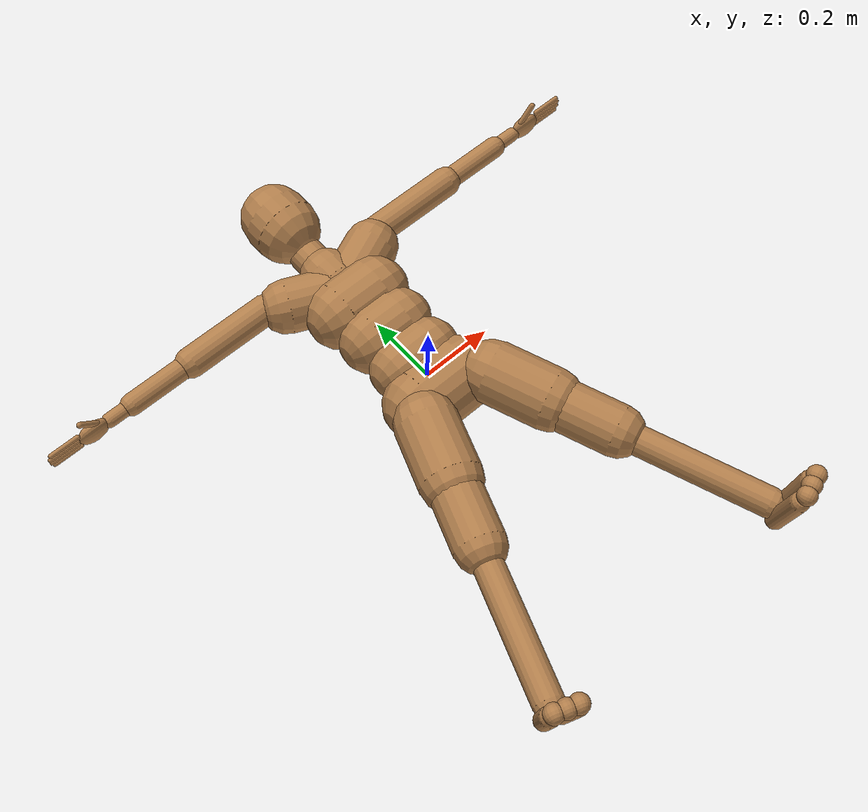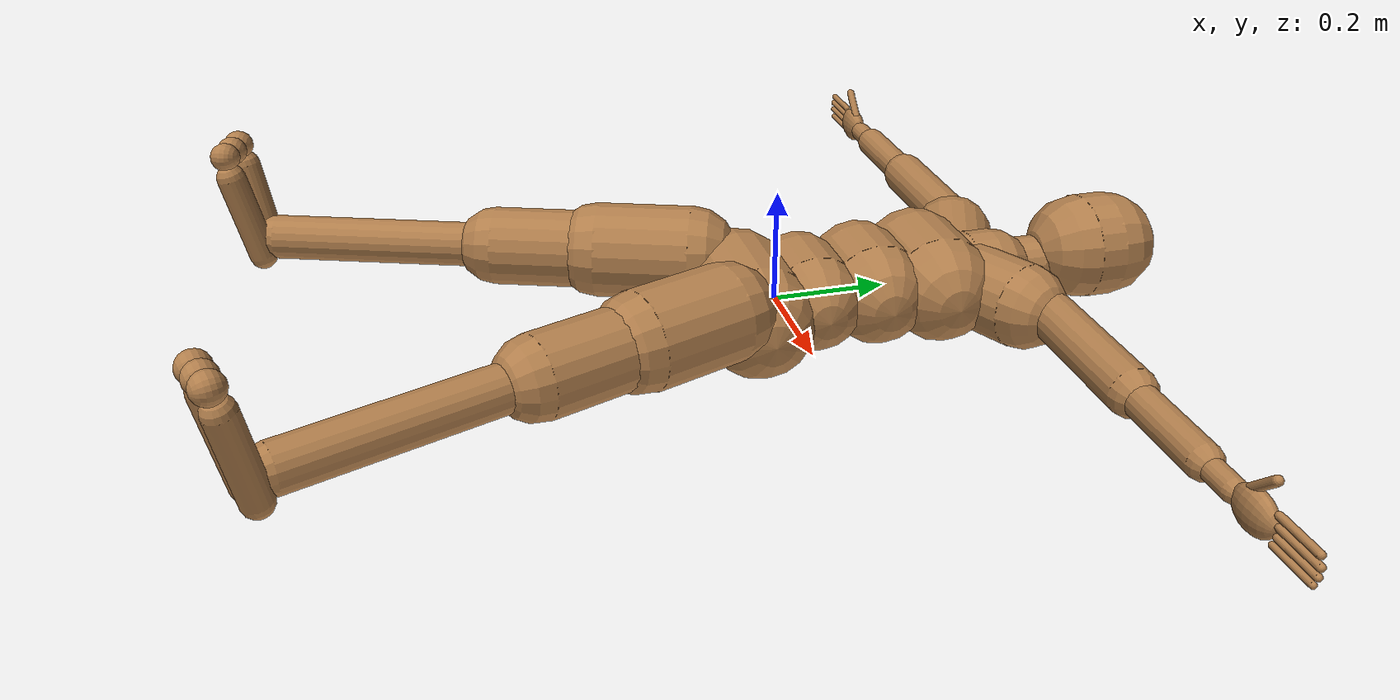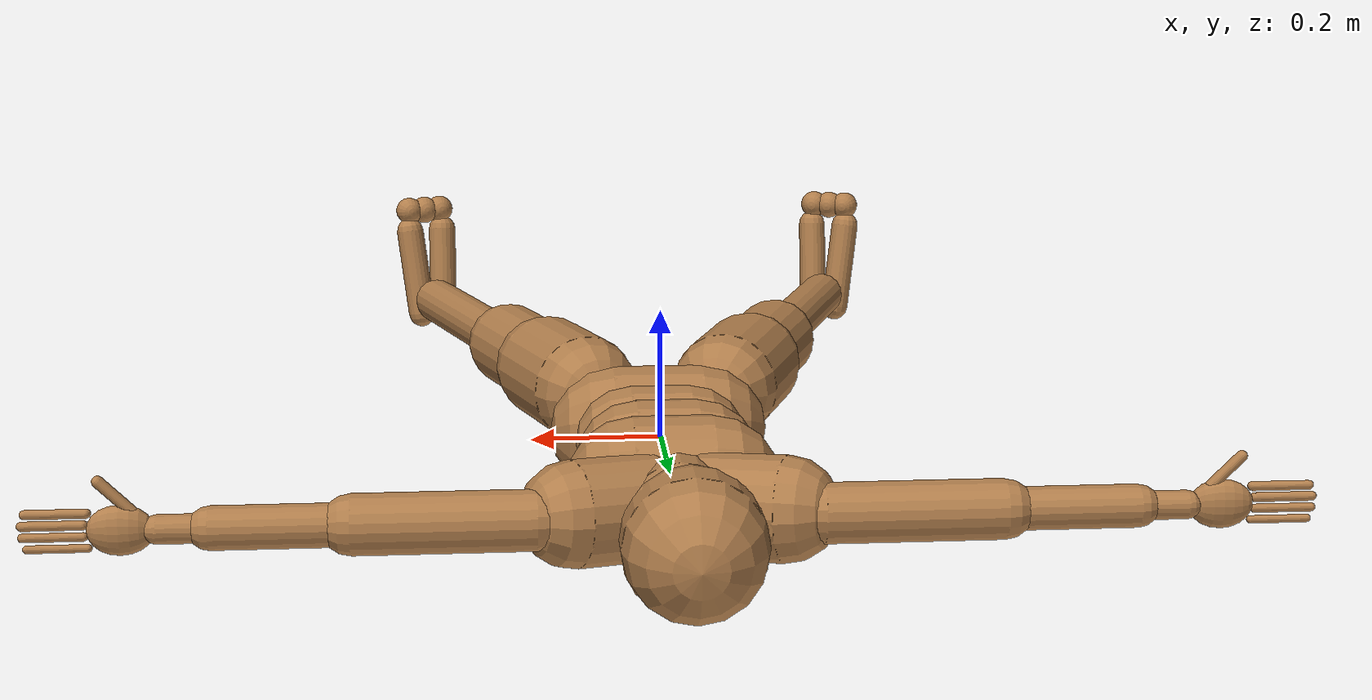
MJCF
<mujoco model="HumanoidCMU Tracking">
  <include file="../common.xml"/>
  <include file="humanoid_CMU_V2020.xml" />
  <size memory="1M"/>

  <custom>
    <numeric name="task_transition" data="1" />
    <numeric name="agent_planner" data="0" />
    <numeric name="agent_horizon" data="0.6" />
    <numeric name="agent_timestep" data="0.015" />
    <numeric name="sampling_spline_points" data="5" />
    <numeric name="sampling_exploration" data="0.15" />
    <numeric name="gradient_spline_points" data="5" />
  </custom>

  <worldbody>
    <body name="mocap-pelvis" mocap="true">
      <site name="mocap-pelvis" type="sphere" size="0.05" group="0" rgba="0 0 1 1" material="target" />
    </body>
    <body name="mocap-head" mocap="true">
      <site name="mocap-head" type="sphere" size="0.03" group="0" rgba="0 0 1 1" material="target" />
    </body>
    <body name="mocap-ltoe" mocap="true">
      <site name="mocap-ltoe" type="sphere" size="0.03" group="0" rgba="0 0 1 1" material="target" />
    </body>
    <body name="mocap-rtoe" mocap="true">
      <site name="mocap-rtoe" type="sphere" size="0.03" group="0" rgba="0 0 1 1" material="target" />
    </body>
    <body name="mocap-lheel" mocap="true">
      <site name="mocap-lheel" type="sphere" size="0.03" group="0" rgba="0 0 1 1" material="target" />
    </body>
    <body name="mocap-rheel" mocap="true">
      <site name="mocap-rheel" type="sphere" size="0.03" group="0" rgba="0 0 1 1" material="target" />
    </body>
    <body name="mocap-lknee" mocap="true">
      <site name="mocap-lknee" type="sphere" size="0.03" group="0" rgba="0 0 1 1" material="target" />
    </body>
    <body name="mocap-rknee" mocap="true">
      <site name="mocap-rknee" type="sphere" size="0.03" group="0" rgba="0 0 1 1" material="target" />
    </body>
    <body name="mocap-lhand" mocap="true">
      <site name="mocap-lhand" type="sphere" size="0.03" group="0" rgba="0 0 1 1" material="target" />
    </body>
    <body name="mocap-rhand" mocap="true">
      <site name="mocap-rhand" type="sphere" size="0.03" group="0" rgba="0 0 1 1" material="target" />
    </body>
    <body name="mocap-lelbow" mocap="true">
      <site name="mocap-lelbow" type="sphere" size="0.03" group="0" rgba="0 0 1 1" material="target" />
    </body>
    <body name="mocap-relbow" mocap="true">
      <site name="mocap-relbow" type="sphere" size="0.03" group="0" rgba="0 0 1 1" material="target" />
    </body>
    <body name="mocap-lshoulder" mocap="true">
      <site name="mocap-lshoulder" type="sphere" size="0.03" group="0" rgba="0 0 1 1" material="target" />
    </body>
    <body name="mocap-rshoulder" mocap="true">
      <site name="mocap-rshoulder" type="sphere" size="0.03" group="0" rgba="0 0 1 1" material="target" />
    </body>
    <body name="mocap-lhip" mocap="true">
      <site name="mocap-lhip" type="sphere" size="0.03" group="0" rgba="0 0 1 1" material="target" />
    </body>
    <body name="mocap-rhip" mocap="true">
      <site name="mocap-rhip" type="sphere" size="0.03" group="0" rgba="0 0 1 1" material="target" />
    </body>
  </worldbody>

  <sensor>
    <user name="control" dim="56" user="0 0.1 0 1.0" />
    <user name="joint vel." dim="56" user="0 0.01 0.0 1.0" />

    <user name="root pos error" dim="3" user="6 10.0 0.0 100.0 0.1" />
    <user name="head pos error" dim="3" user="6 10.0 0.0 100.0 0.1" />
    <user name="ltoe pos error" dim="3" user="6 1.0 0.0 100.0 0.1" />
    <user name="rtoe pos error" dim="3" user="6 1.0 0.0 100.0 0.1" />
    <user name="lheel pos error" dim="3" user="6 1.0 0.0 100.0 0.1" />
    <user name="rheel pos error" dim="3" user="6 1.0 0.0 100.0 0.1" />
    <user name="lknee pos error" dim="3" user="6 10.0 0.0 100.0 0.1" />
    <user name="rknee pos error" dim="3" user="6 10.0 0.0 100.0 0.1" />
    <user name="lhand pos error" dim="3" user="6 1.0 0.0 100.0 0.1" />
    <user name="rhand pos error" dim="3" user="6 1.0 0.0 100.0 0.1" />
    <user name="lelbow pos error" dim="3" user="6 1.0 0.0 100.0 0.1" />
    <user name="relbow pos error" dim="3" user="6 1.0 0.0 100.0 0.1" />
    <user name="lshoulder pos error" dim="3" user="6 10.0 0.0 100.0 0.1" />
    <user name="rshoulder pos error" dim="3" user="6 10.0 0.0 100.0 0.1" />
    <user name="lhip pos error" dim="3" user="6 1.0 0.0 100.0 0.1" />
    <user name="rhip pos error" dim="3" user="6 1.0 0.0 100.0 0.1" />

    <user name="root vel error" dim="3" user="6 10.0 0.0 100.0 0.1" />
    <user name="head vel error" dim="3" user="6 10.0 0.0 100.0 0.1" />
    <user name="ltoe vel error" dim="3" user="6 1.0 0.0 100.0 0.1" />
    <user name="rtoe vel error" dim="3" user="6 1.0 0.0 100.0 0.1" />
    <user name="lheel vel error" dim="3" user="6 1.0 0.0 100.0 0.1" />
    <user name="rheel vel error" dim="3" user="6 1.0 0.0 100.0 0.1" />
    <user name="lknee vel error" dim="3" user="6 10.0 0.0 100.0 0.1" />
    <user name="rknee vel error" dim="3" user="6 10.0 0.0 100.0 0.1" />
    <user name="lhand vel error" dim="3" user="6 1.0 0.0 100.0 0.1" />
    <user name="rhand vel error" dim="3" user="6 1.0 0.0 100.0 0.1" />
    <user name="lelbow vel error" dim="3" user="6 1.0 0.0 100.0 0.1" />
    <user name="relbow vel error" dim="3" user="6 1.0 0.0 100.0 0.1" />
    <user name="lshoulder vel error" dim="3" user="6 10.0 0.0 100.0 0.1" />
    <user name="rshoulder vel error" dim="3" user="6 10.0 0.0 100.0 0.1" />
    <user name="lhip vel error" dim="3" user="6 1.0 0.0 100.0 0.1" />
    <user name="rhip vel error" dim="3" user="6 1.0 0.0 100.0 0.1" />

    <framepos name="trace" objtype="body" objname="root"/>

    <framepos name="tracking_pose[pelvis]" objtype="site" objname="root"/>
    <framepos name="tracking_pose[head]" objtype="body" objname="head_offset"/>
    <framepos name="tracking_pose[ltoe]" objtype="site" objname="ltoes_offset_touch"/>
    <framepos name="tracking_pose[rtoe]" objtype="site" objname="rtoes_offset_touch"/>
    <framepos name="tracking_pose[lheel]" objtype="site" objname="lheel_offset_touch"/>
    <framepos name="tracking_pose[rheel]" objtype="site" objname="rheel_offset_touch"/>
    <framepos name="tracking_pose[lknee]" objtype="geom" objname="ltibia"/>
    <framepos name="tracking_pose[rknee]" objtype="geom" objname="rtibia"/>
    <framepos name="tracking_pose[lhand]" objtype="geom" objname="lwrist"/>
    <framepos name="tracking_pose[rhand]" objtype="geom" objname="rwrist"/>
    <framepos name="tracking_pose[lelbow]" objtype="geom" objname="lradius"/>
    <framepos name="tracking_pose[relbow]" objtype="geom" objname="rradius"/>
    <framepos name="tracking_pose[lshoulder]" objtype="geom" objname="lhumerus"/>
    <framepos name="tracking_pose[rshoulder]" objtype="geom" objname="rhumerus"/>
    <framepos name="tracking_pose[lhip]" objtype="geom" objname="lfemur"/>
    <framepos name="tracking_pose[rhip]" objtype="geom" objname="rfemur"/>

    <framelinvel name="tracking_vel[pelvis]" objtype="site" objname="root"/>
    <framelinvel name="tracking_vel[head]" objtype="body" objname="head_offset"/>
    <framelinvel name="tracking_vel[ltoe]" objtype="site" objname="ltoes_offset_touch"/>
    <framelinvel name="tracking_vel[rtoe]" objtype="site" objname="rtoes_offset_touch"/>
    <framelinvel name="tracking_vel[lheel]" objtype="site" objname="lheel_offset_touch"/>
    <framelinvel name="tracking_vel[rheel]" objtype="site" objname="rheel_offset_touch"/>
    <framelinvel name="tracking_vel[lknee]" objtype="geom" objname="ltibia"/>
    <framelinvel name="tracking_vel[rknee]" objtype="geom" objname="rtibia"/>
    <framelinvel name="tracking_vel[lhand]" objtype="geom" objname="lwrist"/>
    <framelinvel name="tracking_vel[rhand]" objtype="geom" objname="rwrist"/>
    <framelinvel name="tracking_vel[lelbow]" objtype="geom" objname="lradius"/>
    <framelinvel name="tracking_vel[relbow]" objtype="geom" objname="rradius"/>
    <framelinvel name="tracking_vel[lshoulder]" objtype="geom" objname="lhumerus"/>
    <framelinvel name="tracking_vel[rshoulder]" objtype="geom" objname="rhumerus"/>
    <framelinvel name="tracking_vel[lhip]" objtype="geom" objname="lfemur"/>
    <framelinvel name="tracking_vel[rhip]" objtype="geom" objname="rfemur"/>
  </sensor>

  <include file="./keyframes/CMU-CMU-88-88_08_poses.xml" />
</mujoco>

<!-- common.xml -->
<mujoco>

    <visual>
        <headlight ambient=".4 .4 .4" diffuse=".8 .8 .8" specular="0.1 0.1 0.1"/>
        <map znear=".01"/>
        <quality shadowsize="2048"/>
        <global elevation="-15"/>
    </visual>

    <asset>
        <texture name="blue_grid" type="2d" builtin="checker" rgb1=".02 .14 .44" rgb2=".27 .55 1" width="300" height="300" mark="edge" markrgb="1 1 1"/>
        <material name="blue_grid" texture="blue_grid" texrepeat="1 1" texuniform="true" reflectance=".2"/>

        <texture name="grey_grid" type="2d" builtin="checker" rgb1=".26 .26 .26" rgb2=".6 .6 .6" width="300" height="300" mark="edge" markrgb="1 1 1"/>
        <material name="grey_grid" texture="grey_grid" texrepeat="1 1" texuniform="true" reflectance=".2"/>
        <texture name="skybox" type="skybox" builtin="gradient" rgb1=".66 .79 1" rgb2=".9 .91 .93" width="800" height="800"/>

        <material name="self" rgba=".7 .5 .3 1"/>
        <material name="self_default" rgba=".7 .5 .3 1"/>
        <material name="self_highlight" rgba="0 .5 .3 1"/>
        <material name="effector" rgba=".7 .4 .2 1"/>
        <material name="effector_default" rgba=".7 .4 .2 1"/>
        <material name="effector_highlight" rgba="0 .5 .3 1"/>
        <material name="decoration" rgba=".2 .6 .3 1"/>
        <material name="eye" rgba="0 .2 1 1"/>
        <material name="target" rgba=".6 .3 .3 1"/>
        <material name="target_default" rgba=".6 .3 .3 1"/>
        <material name="target_highlight" rgba=".6 .3 .3 .4"/>
        <material name="site" rgba=".5 .5 .5 .3"/>
    </asset>

    <size memory="1M"/>

    <statistic extent="0.4" center="0.3 0.1 0"/>

    <visual>
        <quality shadowsize="8192"/>
        <global azimuth="180" elevation="-30"/>
    </visual>

    <default>
        <geom friction="1.0"/>
    </default>

    <compiler angle="radian" autolimits="true"/>

    <asset>
        <mesh name="apple" file="../../shared_assets/apple/apple.obj" />
        <mesh name="apple_contact0" file="../../shared_assets/apple/contact0.stl"  />
        <mesh name="apple_contact1" file="../../shared_assets/apple/contact1.stl"  />

        <mesh name="doorknob" file="../../shared_assets/doorknob/doorknob.obj" />

        <mesh name="flashlight" file="../../shared_assets/flashlight/flashlight.obj" />
        <mesh name="flashlight_contact0" file="../../shared_assets/flashlight/contact0.stl"  />
        <mesh name="flashlight_contact1" file="../../shared_assets/flashlight/contact1.stl"  />

        <mesh name="hammer" file="../../shared_assets/hammer/hammer.obj" />
        <mesh name="hammer_contact0" file="../../shared_assets/hammer/contact0.stl"  />
        <mesh name="hammer_contact1" file="../../shared_assets/hammer/contact1.stl"  />

        <mesh name="phone" file="../../shared_assets/phone/phone.obj" />
        <mesh name="phone_contact0" file="../../shared_assets/phone/contact0.stl"  />
        <mesh name="phone_contact1" file="../../shared_assets/phone/contact1.stl"  />
        <mesh name="phone_contact2" file="../../shared_assets/phone/contact2.stl"  />

        <mesh name="stapler" file="../../shared_assets/stapler/stapler.obj" />
        <mesh name="stapler_contact0" file="../../shared_assets/stapler/contact0.stl"  />
        <mesh name="stapler_contact1" file="../../shared_assets/stapler/contact1.stl"  />
        <mesh name="stapler_contact2" file="../../shared_assets/stapler/contact2.stl"  />
        <mesh name="stapler_contact3" file="../../shared_assets/stapler/contact3.stl"  />
        <mesh name="stapler_contact4" file="../../shared_assets/stapler/contact4.stl"  />

        <mesh name="waterbottle" file="../../shared_assets/waterbottle/waterbottle.obj" />
        <mesh name="waterbottle_contact0" file="../../shared_assets/waterbottle/contact0.stl"  />
        <mesh name="waterbottle_contact1" file="../../shared_assets/waterbottle/contact1.stl"  />
    </asset>

</mujoco>

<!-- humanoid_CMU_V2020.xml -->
<mujoco model="HumanoidCMU">
  <compiler angle="radian"/>
  <size njmax="500" nconmax="500"/>
  <default>
    <joint limited="true" solimplimit="0 0.99 0.01" stiffness="1" armature=".01" damping="1"/>
    <geom size="0.03 0 0" condim="1" friction="0.7 0.005 0.0001" solref="0.015 1" solimp="0.99 0.99 0.003"/>
    <general ctrllimited="true" ctrlrange="-1 1"/>
    <default class="humanoid">
      <geom type="capsule" material="self" group="2"/>
      <default class="stiff_medium">
        <joint stiffness="10" damping="2"/>
      </default>
      <default class="stiff_medium_higher">
        <joint stiffness="50" damping="4"/>
      </default>
      <default class="stiff_high">
        <joint stiffness="200" damping="5"/>
      </default>
      <default class="sensor_site">
        <site type="sphere" size="0.01" group="4" rgba="1 0 0 .5"/>
      </default>
      <default class="contact">
        <geom condim="3" friction="1. 0.005 0.0001" solref="0.015 1" solimp="0.98 0.98 0.001" priority="1"/>
      </default>
      <default class="tracking_site">
        <site type="sphere" size="0.027" rgba="1 0 0 1" group="3"/>
      </default>
    </default>
  </default>
  <worldbody>
    <body name="root" childclass="humanoid">
      <light name="tracking_light" pos="0 0 7" dir="0 0 -1" mode="trackcom"/>
      <camera name="back" pos="0 3 1.4" xyaxes="-1 0 0 0 -1 2" mode="trackcom"/>
      <camera name="side" pos="-3 0 1.4" xyaxes="0 -1 0 1 0 2" mode="trackcom"/>
      <camera name="front_side" pos="-2 -2 0.5" xyaxes="0.5 -0.5 0 0.1 0.1 1" mode="trackcom"/>
      <camera name="bodycam" pos="0 .3 .1" xyaxes="-1 0 0 0 1 0" fovy="80"/>
      <site name="root" size="0.05" class="tracking_site"/>
      <freejoint/>
      <geom name="root_geom" size="0.1 0.07" pos="0 -0.05 0" quat="1 0 -1 0"/>
      <body name="lhipjoint">
        <geom name="lhipjoint" size="0.008 0.02187363" pos="0.0509685 -0.0459037 0.024723" quat="0.5708 -0.566602 -0.594264 0"/>
        <body name="lfemur" pos="0.101937 -0.0918074 0.0494461" quat="0.984808 0 0 0.173648">
          <site class="tracking_site" name="tracking[lfemur]"/>
          <joint name="lfemurrz" pos="0 0 0" axis="0 0 1" range="-1.0472 1.22173" class="stiff_medium"/>
          <joint name="lfemurry" pos="0 0 0" axis="0 1 0" range="-1.22173 1.22173" class="stiff_medium"/>
          <joint name="lfemurrx" pos="0 0 0" axis="1 0 0" range="-2.79253 0.349066" class="stiff_medium"/>
          <geom name="lfemur_upper" size="0.085 0.083" pos="0 -0.115473 0" quat="0.696364 -0.696364 -0.122788 -0.122788" mass="0"/>
          <geom name="lfemur" size="0.07 0.182226" pos="0 -0.202473 0" quat="0.696364 -0.696364 -0.122788 -0.122788"/>
          <body name="ltibia" pos="0 -0.404945 0">
            <site class="tracking_site" name="tracking[ltibia]"/>
            <joint name="ltibiarx" pos="0 0 0" axis="1 0 0" range="0.01 2.96706"/>
            <geom name="ltibia" size="0.04 0.1825614" pos="0 -0.202846 0" quat="0.696364 -0.696364 -0.122788 -0.122788"/>
            <body name="lfoot" pos="0 -0.415693 0" quat="1 -1 0 0">
              <site class="tracking_site" name="tracking[lfoot]"/>
              <site name="lfoot_touch" type="capsule" pos="0.0 0.02 -0.015" size="0.025 0.01" zaxis="1 0 0" class="sensor_site"/>
              <joint name="lfootrz" pos="0 0 0" axis="0 0 1" range="-1.22173 0.349066" class="stiff_medium"/>
              <joint name="lfootrx" pos="0 0 0" axis="1 0 0" range="-0.785398 0.8" class="stiff_medium"/>
              <geom name="lfoot" size="0.025 0.08" pos="-0.0269999975006 -0.05 -0.0113878" quat=" 0.76725516 -0.64051114  0.02306487 -0.02306583" class="contact"/>
              <geom name="lfoot_ch" size="0.025 0.08" pos="0.0270000024994 -0.05 -0.0113878" quat=" 0.72887266 -0.59399462 -0.24074283 -0.2407425 " class="contact"/>
              <body name="ltoes" pos="0 -0.156372 -0.0227756">
                <site class="tracking_site" name="tracking[ltoes0]"/>
                <joint name="ltoesrx" pos="0 0 0" axis="1 0 0" range="-1.5708 0.349066"/>
                <geom name="ltoes0" type="sphere" size="0.025" pos="0 -0.01 -.01" class="contact"/>
                <geom name="ltoes1" type="sphere" size="0.025" pos=".03 -0.01 -.01" class="contact"/>
                <geom name="ltoes2" type="sphere" size="0.025" pos="-.03 -0.01 -.01" class="contact"/>
                <site name="ltoes_touch" type="capsule" pos="0.0 -0.01 -0.02" size="0.025 0.03" zaxis="1 0 0" class="sensor_site"/>
              </body>
            </body>
          </body>
        </body>
      </body>
      <body name="rhipjoint">
        <geom name="rhipjoint" size="0.008 0.02187363" pos="-0.0509685 -0.0459037 0.024723" quat="0.574856 -0.547594 0.608014 0"/>
        <body name="rfemur" pos="-0.101937 -0.0918074 0.0494461" quat="0.984808 0 0 -0.173648">
          <site class="tracking_site" name="tracking[rfemur]"/>
          <joint name="rfemurrz" pos="0 0 0" axis="0 0 1" range="-1.22173 1.0472" class="stiff_medium"/>
          <joint name="rfemurry" pos="0 0 0" axis="0 1 0" range="-1.22173 1.22173" class="stiff_medium"/>
          <joint name="rfemurrx" pos="0 0 0" axis="1 0 0" range="-2.79253 0.349066" class="stiff_medium"/>
          <geom name="rfemur_upper" size="0.085 0.083" pos="0 -0.115473 0" quat="0.696364 -0.696364 0.122788 0.122788" mass="0"/>
          <geom name="rfemur" size="0.07 0.182226" pos="0 -0.202473 0" quat="0.696364 -0.696364 0.122788 0.122788"/>
          <body name="rtibia" pos="0 -0.404945 0">
            <site class="tracking_site" name="tracking[rtibia]"/>
            <joint name="rtibiarx" pos="0 0 0" axis="1 0 0" range="0.01 2.96706"/>
            <geom name="rtibia" size="0.04 0.1825614" pos="0 -0.202846 0" quat="0.696364 -0.696364 0.122788 0.122788"/>
            <body name="rfoot" pos="0 -0.415693 0" quat="0.707107 -0.707107 0 0">
              <site class="tracking_site" name="tracking[rfoot]"/>
              <site name="rfoot_touch" type="capsule" pos="0.0 0.02 -0.015" size="0.025 0.01" zaxis="1 0 0" class="sensor_site"/>
              <joint name="rfootrz" pos="0 0 0" axis="0 0 1" range="-0.349066 1.22173" class="stiff_medium"/>
              <joint name="rfootrx" pos="0 0 0" axis="1 0 0" range="-0.785398 .8" class="stiff_medium"/>
              <geom name="rfoot" size="0.025 0.08" pos="-0.0269999965316 -0.05 -0.0113878" quat=" 0.73520687 -0.58633523  0.24050108  0.24050079" class="contact"/>
              <geom name="rfoot_ch" size="0.025 0.08" pos="0.0270000034684 -0.05 -0.0113878" quat=" 0.77312469 -0.633231   -0.02545846  0.02545836" class="contact"/>
              <body name="rtoes" pos="0 -0.156372 -0.0227756">
                <site class="tracking_site" name="tracking[rtoes0]"/>
                <joint name="rtoesrx" pos="0 0 0" axis="1 0 0" range="-1.5708 0.349066"/>
                <geom name="rtoes0" type="sphere" size="0.025" pos="0 -0.01 -.01" class="contact"/>
                <geom name="rtoes1" type="sphere" size="0.025" pos=".03 -0.01 -.01" class="contact"/>
                <geom name="rtoes2" type="sphere" size="0.025" pos="-.03 -0.01 -.01" class="contact"/>
                <site name="rtoes_touch" type="capsule" pos="0.0 -0.01 -0.02" size="0.025 0.03" zaxis="1 0 0" class="sensor_site"/>
              </body>
            </body>
          </body>
        </body>
      </body>
      <body name="lowerback">
        <joint name="lowerbackrz" pos="0 0 0" axis="0 0 1" range="-0.523599 0.523599" class="stiff_high"/>
        <joint name="lowerbackry" pos="0 0 0" axis="0 1 0" range="-0.523599 0.523599" class="stiff_high"/>
        <joint name="lowerbackrx" pos="0 0 0" axis="1 0 0" range="-0.349066 0.785398" class="stiff_medium"/>
        <geom name="lowerback" size="0.085 0.04540016" pos="0.00282931 0.0566065 0.01" quat="1 0 1 0"/>
        <body name="upperback" pos="0.000565862 0.113213 -0.00805298">
          <joint name="upperbackrz" pos="0 0 0" axis="0 0 1" range="-0.523599 0.523599" class="stiff_high"/>
          <joint name="upperbackry" pos="0 0 0" axis="0 1 0" range="-0.523599 0.523599" class="stiff_high"/>
          <joint name="upperbackrx" pos="0 0 0" axis="1 0 0" range="-0.349066 0.785398" class="stiff_medium"/>
          <geom name="upperback" size="0.09 0.04542616" pos="0.000256264 0.0567802 0.02" quat="1 0 1 0"/>
          <body name="thorax" pos="0.000512528 0.11356 0.000936821">
            <joint name="thoraxrz" pos="0 0 0" axis="0 0 1" range="-0.523599 0.523599" class="stiff_high"/>
            <joint name="thoraxry" pos="0 0 0" axis="0 1 0" range="-0.523599 0.523599" class="stiff_high"/>
            <joint name="thoraxrx" pos="0 0 0" axis="1 0 0" range="-0.349066 0.785398" class="stiff_medium"/>
            <geom name="thorax" size="0.095 0.0570206" pos="0 0.0569725 0.02" quat="1 0 1 0"/>
            <body name="lowerneck" pos="0 0.113945 0.00468037">
              <joint name="lowerneckrz" pos="0 0 0" axis="0 0 1" range="-0.523599 0.523599" class="stiff_medium_higher"/>
              <joint name="lowerneckry" pos="0 0 0" axis="0 1 0" range="-0.523599 0.523599" class="stiff_medium_higher"/>
              <joint name="lowerneckrx" pos="0 0 0" axis="1 0 0" range="-0.349066 0.785398" class="stiff_medium_higher"/>
              <geom name="lowerneck" size="0.075 0.02279225" pos="-0.00165071 0.0452401 0.00534359" quat="1 1 0 0"/>
              <body name="upperneck" pos="-0.00330143 0.0904801 0.0106872">
                <joint name="upperneckrz" pos="0 0 0" axis="0 0 1" range="-0.523599 0.523599" class="stiff_medium_higher"/>
                <joint name="upperneckry" pos="0 0 0" axis="0 1 0" range="-0.523599 0.523599" class="stiff_medium_higher"/>
                <joint name="upperneckrx" pos="0 0 0" axis="1 0 0" range="-0.349066 0.785398" class="stiff_medium_higher"/>
                <geom name="upperneck" size="0.05 0.0225272" pos="0.000500875 0.0449956 -0.00224644" quat="1 1 0 0"/>
                <body name="head" pos="0.00100175 0.13 -0.00449288">
                  <site class="tracking_site" name="tracking[head]"/>
                  <camera name="egocentric" pos="0 0 0" xyaxes="-1 0 0 0 1 0" fovy="80"/>
                  <joint name="headrz" pos="0 0 0" axis="0 0 1" range="-0.523599 0.523599" class="stiff_medium_higher"/>
                  <joint name="headry" pos="0 0 0" axis="0 1 0" range="-0.523599 0.523599" class="stiff_medium_higher"/>
                  <joint name="headrx" pos="0 0 0" axis="1 0 0" range="-0.349066 0.785398" class="stiff_medium_higher"/>
                  <geom name="head" size="0.095 0.024104" pos="0.000341465 0.048184 0.025" quat="1 1 0 0"/>
                </body>
              </body>
            </body>
            <body name="lclavicle" pos="0 0.113945 0.00468037">
              <joint name="lclaviclerz" pos="0 0 0" axis="0 0 1" range="0 0.349066" class="stiff_high"/>
              <joint name="lclaviclery" pos="0 0 0" axis="0 1 0" range="-0.349066 0.174533" class="stiff_high"/>
              <geom name="lclavicle" size="0.075 0.06" pos="0.0918817 0.0382636 0.00535704" quat="0.688 0.279 -0.67 0"/>
              <body name="lhumerus" pos="0.18 0.09 0.0107141" quat="0.183013 0.683013 -0.683013 0.183013">
                <site class="tracking_site" name="tracking[lhumerus]"/>
                <joint name="lhumerusrz" pos="0 0 0" axis="0 0 1" range="-1.1 1.5708" class="stiff_medium"/>
                <joint name="lhumerusry" pos="0 0 0" axis="0 1 0" range="-1.5708 1.5708" class="stiff_medium"/>
                <joint name="lhumerusrx" pos="0 0 0" axis="1 0 0" range="-1.0472 1.5708" class="stiff_medium"/>
                <site name="lhumerus_ft" class="sensor_site"/>
                <geom name="lhumerus" size="0.042 0.1245789" pos="0 -0.138421 0" quat="0.612372 -0.612372 0.353553 0.353553"/>
                <body name="lradius" pos="0 -0.276843 0">
                  <site class="tracking_site" name="tracking[lradius]"/>
                  <joint name="lradiusrx" pos="0 0 0" axis="1 0 0" range="-0.174533 2.96706"/>
                  <geom name="lradius" size="0.03 0.08169111" pos="0 -0.0907679 0" quat="0.612372 -0.612372 0.353553 0.353553"/>
                  <site name="lwrist" pos="0 -0.181536 0" quat="-0.5 0 0.866025 0"/>
                  <body name="lwrist" pos="0 -0.181536 0" quat="-0.5 0 0.866025 0">
                    <site class="tracking_site" name="tracking[lwrist]"/>
                    <joint name="lwristry" pos="0 0 0" axis="0 1 0" range="0 3.14159"/>
                    <geom name="lwrist" size="0.02 0.03" pos="0 -0.03 0" quat="1.59389e-11 -1.59388e-11 -0.707107 -0.707107"/>
                    <body name="lhand" pos="0 -0.0907676 0">
                      <joint name="lhandrz" pos="0 0 0" axis="0 0 1" range="-0.785398 0.785398"/>
                      <joint name="lhandrx" pos="0 0 0" axis="1 0 0" range="-1.5708 1.5708"/>
                      <site name="lhand_touch" size=".012 0.005 0.015" pos="0 -0.016752 -0.02" quat="0 0 -1 -1" type="ellipsoid" class="sensor_site"/>
                      <geom name="lhand" size="0.035 0.02 0.045" pos="0 -0.016752 0" quat="0 0 -1 -1" type="ellipsoid" class="contact"/>
                      <body name="lfingers" pos="0 -0.075 0">
                        <joint name="lfingersrx" pos="0 0.015 0" axis="1 0 0" range="0 1.5708"/>
                        <site name="lfingers_touch" type="box" size="0.023 0.013 0.003" pos="0 -0.042 -0.007" class="sensor_site"/>
                        <geom name="lfinger0" size="0.0065 0.04" pos="-.024 -0.025 0" quat="1 -1 0 0" class="contact"/>
                        <geom name="lfinger1" size="0.0065 0.04" pos="-.008 -0.03 0" quat="1 -1 0 0" class="contact"/>
                        <geom name="lfinger2" size="0.006 0.04" pos=".008 -0.03 0" quat="1 -1 0 0" class="contact"/>
                        <geom name="lfinger3" size="0.0055 0.04" pos=".024 -0.025 0" quat="1 -1 0 0" class="contact"/>
                      </body>
                      <body name="lthumb" pos="-.025 0 0" quat="0.92388 0 0 -0.382683">
                        <joint name="lthumbrz" pos="0 0 0" axis="0 0 1" range="-0.785398 0.785398"/>
                        <joint name="lthumbrx" pos="0 0 0" axis="1 0 0" range="0 1.57"/>
                        <site name="lthumb_touch" type="box" size="0.006 0.013 0.003" pos="0 -0.043 -0.007" class="sensor_site"/>
                        <geom name="lthumb" size="0.008 0.03" pos="0 -0.03 0" quat="0 0 -1 -1" class="contact"/>
                      </body>
                    </body>
                  </body>
                </body>
              </body>
            </body>
            <body name="rclavicle" pos="0 0.113945 0.00468037">
              <joint name="rclaviclerz" pos="0 0 0" axis="0 0 1" range="-0.349066 0" class="stiff_high"/>
              <joint name="rclaviclery" pos="0 0 0" axis="0 1 0" range="-0.174533 0.349066" class="stiff_high"/>
              <geom name="rclavicle" size="0.075 0.06" pos="-0.0918817 0.0382636 0.00535704" quat="0.688 0.279 0.67 0"/>
              <body name="rhumerus" pos="-0.18 0.09 0.0107141" quat="0.183013 0.683013 0.683013 -0.183013">
                <site class="tracking_site" name="tracking[rhumerus]"/>
                <joint name="rhumerusrz" pos="0 0 0" axis="0 0 1" range="-1.1 1.5708" class="stiff_medium"/>
                <joint name="rhumerusry" pos="0 0 0" axis="0 1 0" range="-1.5708 1.5708" class="stiff_medium"/>
                <joint name="rhumerusrx" pos="0 0 0" axis="1 0 0" range="-1.0472 1.5708" class="stiff_medium"/>
                <site name="rhumerus_ft" class="sensor_site"/>
                <geom name="rhumerus" size="0.042 0.1245789" pos="0 -0.138421 0" quat="0.612372 -0.612372 -0.353553 -0.353553"/>
                <body name="rradius" pos="0 -0.276843 0">
                  <site class="tracking_site" name="tracking[rradius]"/>
                  <joint name="rradiusrx" pos="0 0 0" axis="1 0 0" range="-0.174533 2.96706"/>
                  <geom name="rradius" size="0.03 0.08169111" pos="0 -0.0907679 0" quat="0.61238 -0.612372 -0.353554 -0.353541"/>
                  <body name="rwrist" pos="0 -0.181536 0" quat="-0.5 0 -0.866025 0">
                    <site class="tracking_site" name="tracking[rwrist]"/>
                    <joint name="rwristry" pos="0 0 0" axis="0 1 0" range="-3.14159 0"/>
                    <geom name="rwrist" size="0.02 0.03" pos="0 -0.03 0" quat="0 0 1 1"/>
                    <body name="rhand" pos="0 -0.0907676 0">
                      <joint name="rhandrz" pos="0 0 0" axis="0 0 1" range="-0.785398 0.785398"/>
                      <joint name="rhandrx" pos="0 0 0" axis="1 0 0" range="-1.5708 1.5708"/>
                      <site name="rhand_touch" size=".012 0.005 0.015" pos="0 -0.016752 -0.02" quat="0 0 1 1" type="ellipsoid" class="sensor_site"/>
                      <geom name="rhand" size="0.035 0.02 0.045" pos="0 -0.016752 0" quat="0 0 1 1" type="ellipsoid" class="contact"/>
                      <body name="rfingers" pos="0 -0.075 0">
                        <joint name="rfingersrx" pos="0 0.015 0" axis="1 0 0" range="0 1.5708"/>
                        <site name="rfingers_touch" type="box" size="0.023 0.013 0.003" pos="0 -0.042 -0.007" class="sensor_site"/>
                        <geom name="rfinger0" size="0.0065 0.04" pos=".024 -0.025 0" quat="1 -1 0 0" class="contact"/>
                        <geom name="rfinger1" size="0.0065 0.04" pos=".008 -0.03 0" quat="1 -1 0 0" class="contact"/>
                        <geom name="rfinger2" size="0.006 0.04" pos="-.008 -0.03 0" quat="1 -1 0 0" class="contact"/>
                        <geom name="rfinger3" size="0.0055 0.04" pos="-.024 -0.025 0" quat="1 -1 0 0" class="contact"/>
                      </body>
                      <body name="rthumb" pos=".025 0 0" quat="0.92388 0 0 0.382683">
                        <joint name="rthumbrz" pos="0 0 0" axis="0 0 1" range="-0.785398 0.785398"/>
                        <joint name="rthumbrx" pos="0 0 0" axis="1 0 0" range="0 1.57"/>
                        <site name="rthumb_touch" type="box" size="0.006 0.013 0.003" pos="0 -0.043 -0.007" class="sensor_site"/>
                        <geom name="rthumb" size="0.008 0.03" pos="0 -0.03 0" quat="6.21773e-11 -6.35284e-11 0.707107 0.707107" class="contact"/>
                      </body>
                    </body>
                  </body>
                </body>
              </body>
            </body>
          </body>
        </body>
      </body>
    </body>
  </worldbody>
  <contact>
    <exclude body1="lclavicle" body2="rclavicle"/>
    <exclude body1="lowerneck" body2="lclavicle"/>
    <exclude body1="lowerneck" body2="rclavicle"/>
    <exclude body1="upperneck" body2="lclavicle"/>
    <exclude body1="upperneck" body2="rclavicle"/>
  </contact>
  <actuator>
    <motor name="headrx" joint="headrx" gear="20"/>
    <motor name="headry" joint="headry" gear="20"/>
    <motor name="headrz" joint="headrz" gear="20"/>
    <motor name="lclaviclery" joint="lclaviclery" gear="20"/>
    <motor name="lclaviclerz" joint="lclaviclerz" gear="20"/>
    <motor name="lfemurrx" joint="lfemurrx" gear="120"/>
    <motor name="lfemurry" joint="lfemurry" gear="40"/>
    <motor name="lfemurrz" joint="lfemurrz" gear="40"/>
    <motor name="lfingersrx" joint="lfingersrx" gear="20"/>
    <motor name="lfootrx" joint="lfootrx" gear="20"/>
    <motor name="lfootrz" joint="lfootrz" gear="20"/>
    <motor name="lhandrx" joint="lhandrx" gear="20"/>
    <motor name="lhandrz" joint="lhandrz" gear="20"/>
    <motor name="lhumerusrx" joint="lhumerusrx" gear="40"/>
    <motor name="lhumerusry" joint="lhumerusry" gear="40"/>
    <motor name="lhumerusrz" joint="lhumerusrz" gear="40"/>
    <motor name="lowerbackrx" joint="lowerbackrx" gear="40"/>
    <motor name="lowerbackry" joint="lowerbackry" gear="40"/>
    <motor name="lowerbackrz" joint="lowerbackrz" gear="40"/>
    <motor name="lowerneckrx" joint="lowerneckrx" gear="20"/>
    <motor name="lowerneckry" joint="lowerneckry" gear="20"/>
    <motor name="lowerneckrz" joint="lowerneckrz" gear="20"/>
    <motor name="lradiusrx" joint="lradiusrx" gear="40"/>
    <motor name="lthumbrx" joint="lthumbrx" gear="20"/>
    <motor name="lthumbrz" joint="lthumbrz" gear="20"/>
    <motor name="ltibiarx" joint="ltibiarx" gear="80"/>
    <motor name="ltoesrx" joint="ltoesrx" gear="20"/>
    <motor name="lwristry" joint="lwristry" gear="20"/>
    <motor name="rclaviclery" joint="rclaviclery" gear="20"/>
    <motor name="rclaviclerz" joint="rclaviclerz" gear="20"/>
    <motor name="rfemurrx" joint="rfemurrx" gear="120"/>
    <motor name="rfemurry" joint="rfemurry" gear="40"/>
    <motor name="rfemurrz" joint="rfemurrz" gear="40"/>
    <motor name="rfingersrx" joint="rfingersrx" gear="20"/>
    <motor name="rfootrx" joint="rfootrx" gear="20"/>
    <motor name="rfootrz" joint="rfootrz" gear="20"/>
    <motor name="rhandrx" joint="rhandrx" gear="20"/>
    <motor name="rhandrz" joint="rhandrz" gear="20"/>
    <motor name="rhumerusrx" joint="rhumerusrx" gear="40"/>
    <motor name="rhumerusry" joint="rhumerusry" gear="40"/>
    <motor name="rhumerusrz" joint="rhumerusrz" gear="40"/>
    <motor name="rradiusrx" joint="rradiusrx" gear="40"/>
    <motor name="rthumbrx" joint="rthumbrx" gear="20"/>
    <motor name="rthumbrz" joint="rthumbrz" gear="20"/>
    <motor name="rtibiarx" joint="rtibiarx" gear="80"/>
    <motor name="rtoesrx" joint="rtoesrx" gear="20"/>
    <motor name="rwristry" joint="rwristry" gear="20"/>
    <motor name="thoraxrx" joint="thoraxrx" gear="40"/>
    <motor name="thoraxry" joint="thoraxry" gear="40"/>
    <motor name="thoraxrz" joint="thoraxrz" gear="40"/>
    <motor name="upperbackrx" joint="upperbackrx" gear="40"/>
    <motor name="upperbackry" joint="upperbackry" gear="40"/>
    <motor name="upperbackrz" joint="upperbackrz" gear="40"/>
    <motor name="upperneckrx" joint="upperneckrx" gear="20"/>
    <motor name="upperneckry" joint="upperneckry" gear="20"/>
    <motor name="upperneckrz" joint="upperneckrz" gear="20"/>
  </actuator>
</mujoco>

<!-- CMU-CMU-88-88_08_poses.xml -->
<mujoco>
  <keyframe>
    <key name="home" mpos="0.0 0.0 0.98467 0.00618 -0.015 1.60341 0.02027 0.18664 0.01992 0.00817 -0.1778 0.00093 -0.10203 0.1171 0.05701 -0.10541 -0.09554 0.04172 -0.03679 0.13528 0.48566 -0.05487 -0.1145 0.47273 0.09539 0.26306 0.93651 0.03972 -0.26644 0.90886 -0.06686 0.23087 1.15015 -0.1023 -0.22511 1.14279 -0.03372 0.18345 1.42733 -0.06666 -0.20191 1.41574 0.00271 0.07855 0.88795 -0.00697 -0.06974 0.88417" qpos="0.0 0.0 1.06762 0.46356 0.49205 0.51694 0.52513 -0.35469 0.21726 0.1528 0.16336 0.11251 -1.14696 0.0 0.31186 -0.28587 0.2339 0.0298 -0.29159 -1.02866 0.0 -0.02297 -0.05054 -0.18079 -0.00382 -0.04902 -0.06257 -0.00293 -0.04954 0.06493 -0.00728 0.00262 0.22067 -0.00792 0.00018 0.15609 -0.00265 0.00044 0.06661 -0.08329 -0.08225 1.20076 0.136 -0.66308 0.50011 0.0 0.0 0.0 0.7854 0.0 0.785 0.08247 0.03411 -1.19152 -0.17187 -0.65756 0.42577 0.0 0.0 0.0 0.7854 0.0 0.785" qvel="-0.03423 0.02372 -0.00435 -0.0116 0.35271 -0.14358 0.07902 -0.35085 -0.08474 0.0 -0.04668 -0.05463 -0.16492 0.05454 0.09819 -0.06353 0.0 -0.00243 0.01386 -0.14586 -0.00146 0.01141 -0.0254 -0.02048 0.01134 0.10805 0.02752 -0.01164 0.00131 0.0172 -0.00366 0.00656 0.00662 -0.00134 0.01349 -0.03162 -0.20246 0.357 -0.51514 -0.26834 0.58808 0.0 0.0 0.0 0.0 0.0 0.0 -0.0486 0.23295 -0.40942 0.45545 -0.2097 0.56249 0.0 0.0 0.0 0.0 0.0 0.0" />
    <key mpos="-0.00114 0.00079 0.98453 0.00551 -0.01493 1.604 0.01993 0.18653 0.01973 0.0081 -0.17793 0.00054 -0.10249 0.11716 0.05673 -0.10558 -0.09582 0.04138 -0.03807 0.1357 0.48549 -0.05574 -0.11388 0.47251 0.09361 0.26132 0.93647 0.03948 -0.26362 0.90996 -0.06859 0.23045 1.15034 -0.10346 -0.22333 1.14351 -0.03473 0.18404 1.4276 -0.06751 -0.20136 1.41652 0.00131 0.0794 0.88785 -0.00851 -0.06887 0.884" />
    <key mpos="-0.00141 0.00161 0.98458 0.0047 -0.01463 1.60418 0.0198 0.18649 0.01971 0.00815 -0.17804 0.00073 -0.10267 0.11718 0.0567 -0.10567 -0.09606 0.04145 -0.03906 0.13625 0.48555 -0.05603 -0.11336 0.47264 0.09159 0.26027 0.93581 0.03903 -0.26149 0.91012 -0.07026 0.23054 1.1501 -0.10435 -0.22209 1.14354 -0.03574 0.18463 1.42736 -0.06817 -0.20072 1.41657 0.00098 0.0802 0.88788 -0.00849 -0.0681 0.88407" />
    <key mpos="-0.00158 0.00227 0.98466 0.00388 -0.01432 1.60444 0.01967 0.18639 0.01985 0.0082 -0.17805 0.0008 -0.10284 0.11716 0.05679 -0.10556 -0.09598 0.04149 -0.03992 0.13668 0.48573 -0.05593 -0.11315 0.47269 0.08878 0.26008 0.93423 0.03785 -0.25985 0.9097 -0.07142 0.23035 1.14975 -0.1051 -0.22113 1.1435 -0.03658 0.185 1.42707 -0.06895 -0.20027 1.41657 0.00078 0.08094 0.88804 -0.00867 -0.06736 0.88409" />
    <key mpos="-0.00184 0.00277 0.98465 0.00298 -0.01406 1.60451 0.01965 0.18639 0.01995 0.00842 -0.17797 0.00088 -0.10294 0.11719 0.0567 -0.10531 -0.09579 0.04142 -0.04056 0.13697 0.48571 -0.05568 -0.11275 0.47262 0.0871 0.25916 0.93364 0.03688 -0.2589 0.90892 -0.0723 0.22982 1.14981 -0.10546 -0.22018 1.1431 -0.03741 0.18541 1.42728 -0.06976 -0.19981 1.41626 0.0004 0.08144 0.88802 -0.00909 -0.06685 0.88408" />
    <key mpos="-0.00174 0.00345 0.98474 0.00222 -0.01385 1.60471 0.01963 0.18624 0.01991 0.00847 -0.17807 0.00104 -0.10297 0.11707 0.05669 -0.10533 -0.09598 0.04159 -0.04122 0.13711 0.48577 -0.05571 -0.11254 0.47281 0.08554 0.25842 0.93308 0.03598 -0.2584 0.90856 -0.07313 0.22981 1.14988 -0.10602 -0.21966 1.14295 -0.03794 0.18567 1.42735 -0.07046 -0.19947 1.41614 0.00036 0.08212 0.8881 -0.00869 -0.0662 0.88417" />
    <key mpos="-0.00175 0.00385 0.98465 0.00176 -0.01373 1.60487 0.01933 0.18614 0.01989 0.00839 -0.17807 0.00101 -0.10331 0.11698 0.05655 -0.10548 -0.09607 0.04153 -0.04204 0.13708 0.4857 -0.05585 -0.11238 0.47275 0.08318 0.25839 0.93163 0.03518 -0.25832 0.90831 -0.07354 0.22975 1.14985 -0.10647 -0.21915 1.14283 -0.03829 0.18578 1.42734 -0.07101 -0.1993 1.41607 5e-05 0.08256 0.88803 -0.00867 -0.06579 0.88407" />
    <key mpos="-0.00188 0.00401 0.98466 0.00168 -0.01362 1.60496 0.01926 0.18622 0.01982 0.0086 -0.17801 0.00112 -0.10337 0.11706 0.05653 -0.10524 -0.09587 0.04143 -0.04253 0.1371 0.48574 -0.05616 -0.11203 0.47272 0.08262 0.25868 0.93121 0.03425 -0.25847 0.90796 -0.07363 0.22993 1.14975 -0.10687 -0.21896 1.14275 -0.03849 0.18586 1.42723 -0.07115 -0.19917 1.41596 -0.0002 0.08275 0.88807 -0.00899 -0.06559 0.88406" />
    <key mpos="-0.002 0.00411 0.9847 0.00176 -0.01378 1.60502 0.01905 0.18626 0.01975 0.00861 -0.17801 0.00118 -0.10357 0.11715 0.05657 -0.10524 -0.09587 0.04146 -0.04268 0.13711 0.48578 -0.05608 -0.11197 0.47275 0.08236 0.2586 0.93113 0.03348 -0.25891 0.90786 -0.07386 0.22994 1.1497 -0.10718 -0.21902 1.14286 -0.03847 0.18593 1.42716 -0.07113 -0.19908 1.41601 -0.00036 0.08287 0.88813 -0.00905 -0.06547 0.8841" />
    <key mpos="-0.00198 0.00403 0.98478 0.00243 -0.01433 1.60488 0.01895 0.1862 0.0198 0.00834 -0.17795 0.00127 -0.10368 0.11711 0.05665 -0.10556 -0.0959 0.04158 -0.0426 0.13702 0.48583 -0.05624 -0.11197 0.47286 0.08266 0.2588 0.93136 0.03285 -0.25942 0.90776 -0.07394 0.22999 1.14964 -0.10725 -0.21907 1.14302 -0.03835 0.18597 1.42708 -0.07074 -0.19903 1.4161 -0.00034 0.08276 0.88818 -0.00897 -0.06559 0.88419" />
    <key mpos="-0.00191 0.00392 0.98493 0.00348 -0.01531 1.60451 0.01885 0.18623 0.01996 0.00805 -0.1778 0.00128 -0.10377 0.11714 0.05681 -0.10579 -0.09573 0.04174 -0.04296 0.13691 0.48604 -0.05644 -0.11185 0.47301 0.08306 0.25939 0.93171 0.0323 -0.26007 0.90761 -0.0739 0.23035 1.1497 -0.10712 -0.21935 1.1432 -0.03821 0.18605 1.42708 -0.07011 -0.19898 1.4162 -0.00028 0.08268 0.88835 -0.00883 -0.06567 0.88432" />
    <key mpos="-0.00182 0.00385 0.98495 0.00478 -0.01696 1.60385 0.01791 0.18627 0.01987 0.0082 -0.17781 0.00129 -0.10471 0.1173 0.05696 -0.10553 -0.09558 0.04175 -0.04326 0.13678 0.48611 -0.0566 -0.11204 0.47305 0.08353 0.26021 0.93178 0.03215 -0.26093 0.90733 -0.07364 0.2307 1.14955 -0.1064 -0.2199 1.14338 -0.03796 0.18626 1.42691 -0.069 -0.19884 1.41627 -0.00041 0.08267 0.88842 -0.0086 -0.0657 0.88431" />
    <key mpos="-0.00209 0.00355 0.98487 0.00602 -0.01918 1.60326 0.01735 0.18624 0.01963 0.00823 -0.17778 0.00127 -0.10529 0.11733 0.05678 -0.1055 -0.09553 0.04166 -0.04385 0.13624 0.48596 -0.05718 -0.11231 0.47302 0.08465 0.26193 0.93162 0.03178 -0.26158 0.90719 -0.07282 0.23137 1.14902 -0.10603 -0.22027 1.14362 -0.03747 0.18642 1.42634 -0.0677 -0.19872 1.41634 -0.00111 0.08234 0.88831 -0.00902 -0.06605 0.88426" />
    <key mpos="-0.00216 0.00301 0.98489 0.00727 -0.02171 1.60273 0.01696 0.18638 0.01956 0.00778 -0.17757 0.00132 -0.10563 0.11739 0.05675 -0.10599 -0.0954 0.04175 -0.04435 0.13577 0.48598 -0.05774 -0.11246 0.4731 0.08474 0.26271 0.93137 0.03194 -0.2624 0.90737 -0.07253 0.23172 1.14887 -0.10535 -0.22085 1.14407 -0.03644 0.18651 1.42605 -0.06616 -0.1987 1.41662 -0.00145 0.08175 0.88829 -0.00907 -0.06665 0.88433" />
    <key mpos="-0.00231 0.00237 0.98491 0.00763 -0.0243 1.60239 0.01654 0.18659 0.01953 0.0077 -0.17728 0.00117 -0.10606 0.11764 0.05672 -0.10603 -0.09512 0.04177 -0.04499 0.13534 0.486 -0.05815 -0.11262 0.47314 0.08467 0.26325 0.93095 0.03228 -0.26283 0.90762 -0.0723 0.23224 1.14866 -0.10465 -0.22144 1.14455 -0.03531 0.18662 1.42565 -0.06466 -0.19871 1.41693 -0.0016 0.08101 0.88822 -0.00933 -0.06739 0.88442" />
    <key mpos="-0.00218 0.0018 0.9849 0.0086 -0.02676 1.60209 0.01631 0.18678 0.01947 0.00751 -0.17714 0.00118 -0.10627 0.11779 0.05668 -0.10617 -0.09491 0.04179 -0.04531 0.13495 0.486 -0.05847 -0.1127 0.47318 0.08519 0.26412 0.9311 0.03298 -0.26381 0.90793 -0.07209 0.23272 1.14853 -0.10372 -0.22236 1.14499 -0.03382 0.18654 1.42526 -0.06304 -0.19883 1.4172 -0.00158 0.08035 0.88815 -0.00933 -0.06805 0.88448" />
    <key mpos="-0.00171 0.00131 0.98488 0.00985 -0.02872 1.60181 0.01607 0.18695 0.01936 0.00695 -0.17711 0.00123 -0.10646 0.11794 0.05668 -0.10678 -0.09498 0.04188 -0.04521 0.13457 0.48598 -0.05902 -0.11278 0.47326 0.08355 0.26402 0.92948 0.03391 -0.2646 0.9081 -0.07113 0.23256 1.14875 -0.1024 -0.22287 1.14533 -0.03219 0.18641 1.42539 -0.06173 -0.199 1.41752 -0.0014 0.07984 0.8881 -0.00879 -0.06859 0.88449" />
    <key mpos="-0.00154 0.00053 0.98482 0.01084 -0.03019 1.60157 0.01645 0.18709 0.01921 0.00686 -0.1768 0.00131 -0.10601 0.11793 0.05648 -0.10691 -0.09471 0.04192 -0.04546 0.13432 0.48589 -0.05941 -0.11307 0.47331 0.08235 0.26405 0.92788 0.03498 -0.26568 0.90798 -0.07022 0.23267 1.14864 -0.10128 -0.22358 1.14517 -0.0307 0.1862 1.42515 -0.06061 -0.19915 1.4173 -0.0016 0.07888 0.88791 -0.00916 -0.06954 0.8846" />
    <key mpos="-0.00033 0.00044 0.98483 0.01233 -0.03138 1.60125 0.01603 0.18735 0.0194 0.0061 -0.17669 0.0013 -0.10637 0.11812 0.05672 -0.10755 -0.0945 0.04205 -0.04538 0.13412 0.48607 -0.05964 -0.11275 0.47339 0.08182 0.2638 0.9273 0.03626 -0.26619 0.90794 -0.06958 0.23234 1.14886 -0.10039 -0.22378 1.14486 -0.02906 0.18586 1.42522 -0.05948 -0.19942 1.41697 -0.00053 0.07893 0.88802 -0.0076 -0.06951 0.88449" />
    <key mpos="0.00038 9e-05 0.98471 0.01357 -0.03251 1.60108 0.01565 0.18771 0.01936 0.0056 -0.17647 0.00115 -0.10674 0.1185 0.05678 -0.10797 -0.09423 0.04202 -0.04492 0.13401 0.48604 -0.05959 -0.11289 0.47329 0.08179 0.26316 0.92676 0.03738 -0.26631 0.90751 -0.06871 0.23176 1.14893 -0.09932 -0.22411 1.14443 -0.02736 0.18526 1.42516 -0.05837 -0.19996 1.41655 0.00011 0.07863 0.88794 -0.00712 -0.0698 0.88435" />
    <key mpos="0.00103 -8e-05 0.9847 0.015 -0.03356 1.60097 0.01541 0.18792 0.01936 0.00514 -0.17648 0.00108 -0.10688 0.11859 0.05688 -0.10839 -0.09426 0.04212 -0.04438 0.13383 0.48605 -0.05948 -0.11302 0.47333 0.08326 0.26223 0.9275 0.03818 -0.26631 0.90723 -0.06813 0.2315 1.14917 -0.09874 -0.22434 1.14407 -0.02573 0.18455 1.42516 -0.05722 -0.20058 1.41613 0.00075 0.07846 0.88794 -0.00673 -0.06996 0.88435" />
    <key mpos="0.00216 -0.00027 0.9846 0.01602 -0.03441 1.60071 0.01516 0.1882 0.01941 0.00475 -0.17611 0.00091 -0.10705 0.11878 0.05702 -0.10877 -0.09397 0.0421 -0.04411 0.13379 0.48614 -0.05907 -0.11302 0.4732 0.08342 0.26076 0.92642 0.03855 -0.2663 0.90643 -0.06671 0.23092 1.14905 -0.09789 -0.22475 1.14361 -0.02475 0.18379 1.42509 -0.0561 -0.20131 1.41567 0.00169 0.07841 0.88795 -0.00576 -0.07001 0.88416" />
    <key mpos="0.00333 -0.00084 0.98457 0.01654 -0.03528 1.60082 0.01491 0.18836 0.01956 0.00445 -0.17587 0.00085 -0.10727 0.11889 0.0572 -0.10902 -0.09375 0.04225 -0.04388 0.13375 0.48625 -0.05837 -0.11331 0.47322 0.0845 0.25958 0.92624 0.03891 -0.26611 0.90564 -0.06549 0.23049 1.14907 -0.09709 -0.22523 1.14319 -0.02353 0.18292 1.42503 -0.05535 -0.2021 1.41528 0.00274 0.07781 0.88789 -0.00474 -0.07061 0.88417" />
    <key mpos="0.00498 -0.0012 0.98438 0.01724 -0.03652 1.60037 0.01466 0.18842 0.01946 0.00451 -0.17578 0.00078 -0.10743 0.11891 0.05727 -0.10903 -0.09378 0.04223 -0.04318 0.13346 0.4862 -0.05769 -0.11345 0.47312 0.08681 0.25796 0.92634 0.03938 -0.26638 0.90478 -0.06364 0.2291 1.14889 -0.09627 -0.22569 1.14256 -0.02218 0.18177 1.42497 -0.05457 -0.2032 1.41471 0.00415 0.07752 0.88776 -0.00279 -0.07092 0.88392" />
    <key mpos="0.00648 -0.00175 0.98407 0.01794 -0.03742 1.59971 0.01457 0.18859 0.01927 0.00399 -0.17567 0.00035 -0.10742 0.11896 0.05719 -0.10929 -0.09351 0.04218 -0.04281 0.13326 0.48608 -0.05672 -0.11419 0.47287 0.0896 0.25641 0.92621 0.03976 -0.26726 0.90395 -0.06152 0.22812 1.14838 -0.09541 -0.22663 1.14202 -0.0208 0.18072 1.42455 -0.05365 -0.20418 1.41416 0.00546 0.077 0.88748 -0.00155 -0.07143 0.88361" />
    <key mpos="0.00829 -0.00173 0.98401 0.01799 -0.03776 1.59942 0.01455 0.18857 0.01942 0.00398 -0.17564 0.00047 -0.10735 0.11881 0.05739 -0.10927 -0.09346 0.04231 -0.04245 0.13306 0.48624 -0.05524 -0.11407 0.47282 0.09195 0.25443 0.92559 0.0399 -0.26858 0.90365 -0.05866 0.22744 1.14827 -0.09476 -0.22716 1.14187 -0.01942 0.1799 1.42463 -0.05321 -0.20501 1.41407 0.00711 0.07715 0.88753 0.00084 -0.07131 0.88344" />
    <key mpos="0.01009 -0.00186 0.98397 0.01815 -0.03748 1.59928 0.01464 0.18869 0.0195 0.00397 -0.17563 0.00044 -0.10721 0.1189 0.05759 -0.10919 -0.09343 0.0425 -0.04186 0.13281 0.48638 -0.05415 -0.11404 0.47289 0.09793 0.25312 0.92547 0.03928 -0.2719 0.90367 -0.05387 0.22894 1.14766 -0.09419 -0.22796 1.14211 -0.01733 0.1789 1.42395 -0.05276 -0.20593 1.41434 0.00902 0.07707 0.88752 0.00327 -0.07141 0.88333" />
    <key mpos="0.01123 -0.00223 0.98364 0.01852 -0.03702 1.59842 0.01474 0.18885 0.01901 0.00477 -0.17587 8e-05 -0.10702 0.11912 0.05749 -0.10838 -0.09371 0.04225 -0.04103 0.13283 0.48618 -0.0527 -0.11468 0.47253 0.10934 0.25377 0.92565 0.03725 -0.2785 0.90296 -0.0447 0.23161 1.14651 -0.09336 -0.2301 1.14212 -0.01459 0.17761 1.42283 -0.05262 -0.20703 1.41436 0.01002 0.07678 0.88727 0.00481 -0.07172 0.88293" />
    <key mpos="0.0119 -0.00245 0.98365 0.01987 -0.03614 1.59722 0.01559 0.18863 0.01877 0.00572 -0.17634 0.0 -0.106 0.11864 0.05732 -0.10744 -0.09426 0.04231 -0.04119 0.13212 0.4862 -0.0507 -0.11518 0.47246 0.12775 0.25707 0.92924 0.03303 -0.2914 0.90415 -0.03138 0.23572 1.14654 -0.09382 -0.23425 1.1434 -0.01162 0.17622 1.42266 -0.05262 -0.20829 1.41531 0.01037 0.07657 0.88729 0.0063 -0.07196 0.88291" />
    <key mpos="0.01216 -0.00204 0.98403 0.02121 -0.03443 1.59621 0.01617 0.1885 0.01856 0.00683 -0.17618 5e-05 -0.10524 0.1184 0.05748 -0.10641 -0.09438 0.04268 -0.04277 0.13169 0.48672 -0.04872 -0.11523 0.47271 0.15209 0.26033 0.9352 0.02393 -0.31165 0.90589 -0.01308 0.23861 1.14791 -0.09463 -0.2417 1.14599 -0.00904 0.17508 1.42382 -0.05203 -0.20947 1.41702 0.00993 0.07712 0.8878 0.00784 -0.07144 0.88315" />
    <key mpos="0.01144 -0.00145 0.9852 0.02217 -0.03279 1.59572 0.01639 0.18874 0.01893 0.00731 -0.17569 0.0002 -0.1047 0.11839 0.05837 -0.10579 -0.09416 0.04372 -0.04421 0.13158 0.4879 -0.04638 -0.11475 0.47352 0.18308 0.26344 0.94819 0.00796 -0.33871 0.9115 0.00603 0.2412 1.15107 -0.09924 -0.25277 1.15175 -0.00729 0.17372 1.42574 -0.05111 -0.21094 1.42053 0.00831 0.07785 0.88911 0.00848 -0.07072 0.88417" />
    <key mpos="0.00955 -0.00015 0.98705 0.02391 -0.03076 1.59586 0.01678 0.18904 0.01935 0.0083 -0.17559 0.00111 -0.10382 0.11838 0.05974 -0.10468 -0.09438 0.04549 -0.04558 0.1326 0.48954 -0.04372 -0.11491 0.47508 0.21444 0.26312 0.96494 -0.01601 -0.37195 0.92142 0.02451 0.24304 1.15605 -0.10767 -0.26646 1.16031 -0.00588 0.17293 1.4287 -0.05062 -0.21179 1.42501 0.00511 0.07917 0.89103 0.0081 -0.06936 0.88596" />
    <key mpos="0.0068 0.00151 0.98957 0.02667 -0.0285 1.59655 0.01712 0.18925 0.02055 0.00959 -0.17535 0.00212 -0.10314 0.11857 0.06188 -0.10328 -0.09463 0.04769 -0.04693 0.13402 0.49191 -0.04085 -0.11495 0.47708 0.24471 0.25817 0.98378 -0.04628 -0.40827 0.93641 0.04198 0.24451 1.16187 -0.11896 -0.28084 1.1711 -0.00406 0.17254 1.43183 -0.05118 -0.21199 1.4299 0.00098 0.08106 0.89381 0.00674 -0.06737 0.88824" />
    <key mpos="0.00245 0.0033 0.99256 0.03082 -0.0264 1.59765 0.01724 0.18967 0.02156 0.01141 -0.17525 0.00319 -0.10231 0.11868 0.06441 -0.10129 -0.09513 0.05024 -0.04811 0.1361 0.49463 -0.03787 -0.11516 0.4795 0.27048 0.24899 1.00269 -0.08281 -0.44322 0.95688 0.05677 0.24558 1.16796 -0.13315 -0.29404 1.1845 -0.00164 0.17226 1.43515 -0.05072 -0.21205 1.43509 -0.00489 0.083 0.89703 0.00372 -0.06528 0.89103" />
    <key mpos="-0.00362 0.00477 0.99573 0.03601 -0.02459 1.59882 0.01791 0.1902 0.0231 0.01415 -0.17563 0.00527 -0.10135 0.11939 0.06704 -0.09954 -0.09733 0.05296 -0.04955 0.13853 0.49748 -0.03447 -0.1158 0.48204 0.29082 0.23723 1.01963 -0.12445 -0.47303 0.9817 0.06885 0.24534 1.17344 -0.14975 -0.30478 1.19999 0.00133 0.1721 1.4385 -0.05067 -0.21181 1.44051 -0.01217 0.08452 0.90034 -0.00169 -0.06363 0.89409" />
    <key mpos="-0.01146 0.00611 0.9992 0.04175 -0.02277 1.59983 0.0174 0.19093 0.02495 0.01718 -0.17669 0.00798 -0.10217 0.12151 0.07024 -0.09814 -0.10129 0.05644 -0.04986 0.1418 0.50056 -0.02942 -0.1172 0.48506 0.30474 0.22315 1.03162 -0.16614 -0.49597 1.00999 0.07846 0.24349 1.17784 -0.16707 -0.31233 1.21705 0.00468 0.1724 1.44181 -0.05141 -0.21091 1.4465 -0.02092 0.08579 0.90385 -0.00902 -0.06224 0.89754" />
    <key mpos="-0.02119 0.00851 1.00145 0.04786 -0.0241 1.59592 0.01425 0.19224 0.02789 0.01931 -0.17968 0.00965 -0.10687 0.12556 0.07323 -0.09726 -0.10686 0.05906 -0.04941 0.14609 0.50288 -0.02575 -0.11967 0.48732 0.31269 0.20989 1.03957 -0.20545 -0.51311 1.03798 0.08282 0.24274 1.17771 -0.18067 -0.31739 1.23209 0.00586 0.17084 1.44054 -0.05137 -0.21121 1.4519 -0.03472 0.08832 0.90669 -0.02136 -0.05955 0.89957" />
    <key mpos="-0.03358 0.00906 1.0033 0.05573 -0.02198 1.59327 0.01358 0.19404 0.03013 0.02149 -0.1809 0.01311 -0.10934 0.13173 0.07676 -0.09815 -0.11353 0.06289 -0.04434 0.15179 0.50536 -0.01798 -0.12105 0.48974 0.31414 0.19664 1.03865 -0.24443 -0.52113 1.06544 0.08604 0.24073 1.17658 -0.19864 -0.31918 1.24906 0.01011 0.1717 1.44048 -0.05279 -0.20916 1.45626 -0.04821 0.08879 0.90863 -0.03392 -0.059 0.90141" />
    <key mpos="-0.04825 0.00876 1.00339 0.06513 -0.01955 1.58779 0.01345 0.19703 0.03326 0.02467 -0.18232 0.01808 -0.11237 0.14096 0.0801 -0.09813 -0.11954 0.06617 -0.03748 0.15609 0.50729 -0.00932 -0.12132 0.49138 0.31034 0.18383 1.03056 -0.27982 -0.52231 1.08892 0.08663 0.23989 1.1713 -0.21583 -0.31741 1.26362 0.01552 0.17275 1.43703 -0.05447 -0.20666 1.45858 -0.06394 0.0886 0.90898 -0.04927 -0.05913 0.9014" />
    <key mpos="-0.06526 0.00849 1.0007 0.07545 -0.01657 1.57747 0.015 0.20264 0.03567 0.02927 -0.18337 0.02347 -0.11479 0.15537 0.08139 -0.09622 -0.12437 0.06932 -0.0324 0.15949 0.50744 0.00157 -0.12153 0.49254 0.30226 0.17287 1.01393 -0.31128 -0.51844 1.10731 0.08468 0.23815 1.16019 -0.23149 -0.31247 1.27407 0.02159 0.17389 1.42864 -0.05467 -0.20388 1.45642 -0.08107 0.08846 0.90644 -0.06738 -0.05935 0.89869" />
    <key mpos="-0.08391 0.00823 0.99396 0.08711 -0.01305 1.5602 0.01673 0.21147 0.03624 0.03254 -0.18426 0.02765 -0.11714 0.17447 0.0796 -0.09515 -0.12936 0.07252 -0.02958 0.16407 0.50451 0.01348 -0.12285 0.49305 0.29055 0.16312 0.98951 -0.33977 -0.51155 1.12025 0.08055 0.23707 1.14258 -0.24456 -0.30581 1.27902 0.02842 0.1755 1.414 -0.05331 -0.2006 1.44832 -0.09886 0.08821 0.89956 -0.08809 -0.05986 0.89217" />
    <key mpos="-0.10443 0.00799 0.98273 0.09904 -0.00939 1.53557 0.0182 0.21984 0.03406 0.03644 -0.18616 0.03034 -0.11788 0.18937 0.07555 -0.09285 -0.13509 0.07516 -0.02573 0.1705 0.49919 0.0243 -0.12696 0.49336 0.27674 0.15447 0.95827 -0.36571 -0.5032 1.12654 0.07502 0.23676 1.11808 -0.25667 -0.29873 1.27788 0.03581 0.17716 1.3921 -0.05246 -0.19678 1.43349 -0.11843 0.08776 0.88801 -0.11189 -0.0606 0.88147" />
    <key mpos="-0.12641 0.00854 0.9669 0.11053 -0.0063 1.50384 0.01973 0.22346 0.03039 0.0392 -0.18891 0.03106 -0.11622 0.19199 0.07157 -0.09128 -0.13963 0.0744 -0.01714 0.17736 0.49382 0.02984 -0.13221 0.49149 0.26048 0.14598 0.91977 -0.38993 -0.49389 1.12609 0.06849 0.23741 1.08643 -0.26826 -0.29127 1.27009 0.04305 0.17808 1.36213 -0.05213 -0.19333 1.41154 -0.14151 0.08818 0.87223 -0.1376 -0.0603 0.86615" />
    <key mpos="-0.14884 0.00989 0.94697 0.12057 -0.00403 1.46593 0.02252 0.22661 0.02591 0.04078 -0.19001 0.02964 -0.11252 0.1912 0.06687 -0.08943 -0.13733 0.06967 -0.00927 0.18556 0.48834 0.03113 -0.13794 0.48699 0.24193 0.13852 0.87345 -0.41218 -0.48366 1.11893 0.06132 0.2368 1.04871 -0.27847 -0.2831 1.25493 0.04996 0.17804 1.32547 -0.05186 -0.19023 1.38274 -0.16678 0.08893 0.8523 -0.16324 -0.05958 0.84707" />
    <key mpos="-0.17075 0.01131 0.92352 0.13 -0.00192 1.42261 0.0251 0.23268 0.02236 0.04235 -0.19345 0.02731 -0.10865 0.19179 0.06248 -0.08645 -0.13625 0.06565 -0.00257 0.19784 0.48324 0.03382 -0.1454 0.48295 0.22078 0.13177 0.8208 -0.4344 -0.4705 1.10579 0.05399 0.23624 1.0059 -0.28784 -0.27431 1.23474 0.05555 0.17801 1.283 -0.05162 -0.18703 1.34827 -0.19134 0.08925 0.82847 -0.18808 -0.05932 0.8249" />
    <key mpos="-0.19061 0.01213 0.89602 0.1366 0.0002 1.37498 0.02574 0.24956 0.01987 0.04275 -0.20518 0.02739 -0.10354 0.19479 0.05803 -0.08173 -0.13796 0.06372 0.00344 0.21531 0.4781 0.03903 -0.15734 0.48053 0.19766 0.12673 0.76378 -0.45459 -0.45527 1.08598 0.04511 0.23446 0.95902 -0.2969 -0.26385 1.20881 0.0601 0.17757 1.23599 -0.05322 -0.18332 1.31103 -0.21267 0.08921 0.80061 -0.21142 -0.05942 0.79876" />
    <key mpos="-0.20669 0.01215 0.86389 0.14018 0.00129 1.32457 0.01354 0.29068 0.01864 0.03338 -0.23217 0.0298 -0.09708 0.20362 0.05542 -0.07746 -0.14296 0.06281 0.01016 0.24135 0.47423 0.04552 -0.17646 0.47806 0.17347 0.1236 0.70484 -0.47313 -0.43956 1.06024 0.03613 0.23246 0.91048 -0.30673 -0.25248 1.17818 0.06372 0.17591 1.18655 -0.05699 -0.18013 1.27148 -0.22867 0.08844 0.76783 -0.23031 -0.0602 0.76786" />
    <key mpos="-0.21978 0.01307 0.82646 0.14063 0.002 1.27368 0.01356 0.30068 0.01574 0.02826 -0.24851 0.03216 -0.09244 0.20941 0.05578 -0.0721 -0.14744 0.06448 0.01476 0.27323 0.47143 0.05403 -0.20083 0.4767 0.15061 0.123 0.64363 -0.4926 -0.42288 1.02797 0.02855 0.22935 0.85994 -0.31789 -0.24112 1.14215 0.06492 0.17419 1.13528 -0.0635 -0.17694 1.22862 -0.24171 0.08871 0.72987 -0.24428 -0.05991 0.73113" />
    <key mpos="-0.22902 0.01478 0.78448 0.13679 0.00161 1.22358 0.01728 0.30649 0.01419 0.02904 -0.25661 0.03534 -0.08539 0.2125 0.05654 -0.06549 -0.15063 0.06946 0.02162 0.30199 0.46748 0.06591 -0.22265 0.47717 0.13138 0.1254 0.58167 -0.51377 -0.40502 0.98761 0.02283 0.22563 0.80787 -0.33114 -0.23037 1.10049 0.06351 0.17106 1.08272 -0.07361 -0.17429 1.18319 -0.24931 0.09007 0.68727 -0.25293 -0.05852 0.68925" />
    <key mpos="-0.236 0.01611 0.7398 0.12919 0.00101 1.17505 0.02202 0.30755 0.01461 0.03204 -0.25912 0.04054 -0.07915 0.21244 0.05805 -0.06157 -0.15247 0.07513 0.03241 0.3216 0.46297 0.07995 -0.23492 0.47745 0.11848 0.13003 0.52136 -0.53384 -0.3879 0.94006 0.02002 0.22125 0.75585 -0.34631 -0.21902 1.0537 0.06148 0.1672 1.03068 -0.08769 -0.17069 1.1379 -0.25291 0.09039 0.64116 -0.25813 -0.05812 0.64486" />
    <key mpos="-0.24057 0.01658 0.69337 0.11966 -0.00264 1.12779 0.02706 0.30788 0.01675 0.03586 -0.26132 0.04708 -0.07344 0.21205 0.06017 -0.05792 -0.1546 0.08095 0.05058 0.32908 0.45923 0.0967 -0.23877 0.47805 0.11398 0.13535 0.46353 -0.55251 -0.37076 0.8849 0.02311 0.21638 0.70473 -0.36325 -0.20778 1.00414 0.06036 0.16029 0.97976 -0.10484 -0.16802 1.0933 -0.25174 0.08969 0.59305 -0.25917 -0.05868 0.59849" />
    <key mpos="-0.2433 0.01805 0.64549 0.10572 -0.00621 1.08322 0.03292 0.30773 0.02101 0.0413 -0.26314 0.05373 -0.06646 0.21042 0.06371 -0.05298 -0.15656 0.08667 0.0723 0.32937 0.4573 0.11239 -0.23852 0.47989 0.12155 0.1404 0.40975 -0.57183 -0.35161 0.82458 0.02998 0.20861 0.65462 -0.38161 -0.19455 0.95007 0.05718 0.15248 0.93082 -0.12479 -0.1653 1.04752 -0.24696 0.09024 0.54396 -0.25643 -0.05797 0.5503" />
    <key mpos="-0.24273 0.01987 0.59558 0.08721 -0.01144 1.04142 0.03961 0.30768 0.02657 0.04674 -0.26522 0.06156 -0.05876 0.20879 0.06795 -0.04814 -0.15881 0.09328 0.09421 0.32597 0.45679 0.12623 -0.2385 0.48306 0.14129 0.14372 0.3645 -0.59414 -0.32934 0.76199 0.03996 0.19947 0.60868 -0.40242 -0.17811 0.89228 0.05181 0.14415 0.88613 -0.14912 -0.16234 1.00136 -0.23691 0.09 0.49271 -0.2488 -0.05794 0.50112" />
    <key mpos="-0.23814 0.02188 0.54309 0.06197 -0.01751 1.00342 0.04708 0.30724 0.03365 0.05136 -0.2677 0.06981 -0.05132 0.20781 0.07365 -0.04414 -0.1616 0.1007 0.11424 0.32065 0.45859 0.13527 -0.24164 0.48812 0.18107 0.14249 0.33428 -0.62195 -0.30319 0.69751 0.05679 0.18849 0.56973 -0.42549 -0.1597 0.82946 0.04294 0.13628 0.84768 -0.17894 -0.15877 0.95405 -0.22154 0.08933 0.43962 -0.23685 -0.05814 0.45031" />
    <key mpos="-0.22967 0.02441 0.49046 0.03169 -0.02298 0.96833 0.05408 0.30504 0.04072 0.05272 -0.27068 0.078 -0.04477 0.20594 0.08044 -0.04257 -0.16417 0.10815 0.13119 0.31506 0.46183 0.13932 -0.24692 0.49384 0.24545 0.13909 0.32629 -0.65628 -0.2733 0.62968 0.09006 0.18232 0.54304 -0.45229 -0.14362 0.76447 0.02993 0.12864 0.81448 -0.2121 -0.15606 0.90037 -0.20056 0.08901 0.38794 -0.21994 -0.05786 0.40019" />
    <key mpos="-0.21839 0.02572 0.44291 -0.01303 -0.03093 0.94383 0.06061 0.29999 0.04708 0.0536 -0.27161 0.08635 -0.03869 0.20082 0.08545 -0.04213 -0.16498 0.11459 0.14576 0.30864 0.46317 0.14158 -0.24962 0.49901 0.33497 0.13577 0.36991 -0.69283 -0.23496 0.56388 0.12973 0.17411 0.54138 -0.48044 -0.11799 0.69732 0.01074 0.11853 0.79223 -0.25752 -0.14836 0.85761 -0.17622 0.08809 0.34359 -0.19958 -0.05822 0.35565" />
    <key mpos="-0.20484 0.02784 0.40519 -0.07057 -0.04099 0.92813 0.0656 0.29722 0.05215 0.05491 -0.27146 0.0938 -0.03372 0.19814 0.0907 -0.04116 -0.16467 0.12023 0.16231 0.30476 0.4629 0.1467 -0.24502 0.50355 0.42238 0.12944 0.48993 -0.73704 -0.18905 0.49992 0.17265 0.16347 0.58726 -0.51275 -0.09756 0.63381 -0.01888 0.10779 0.78823 -0.30916 -0.14261 0.815 -0.14982 0.08942 0.31185 -0.1768 -0.05649 0.32084" />
    <key mpos="-0.19175 0.03123 0.38404 -0.14334 -0.05383 0.92262 0.07071 0.29811 0.05613 0.05726 -0.27142 0.09945 -0.02681 0.19765 0.09572 -0.03829 -0.16389 0.12475 0.18612 0.30141 0.45934 0.16075 -0.23144 0.50489 0.45795 0.11714 0.69247 -0.78488 -0.13472 0.44101 0.19005 0.15199 0.68841 -0.55176 -0.0804 0.57994 -0.06211 0.09342 0.80314 -0.36676 -0.13898 0.77654 -0.12628 0.09376 0.29839 -0.15557 -0.05194 0.30166" />
    <key mpos="-0.18439 0.03601 0.38417 -0.23175 -0.06775 0.92507 0.07401 0.29907 0.05852 0.06137 -0.27123 0.10259 -0.01918 0.19593 0.10148 -0.03242 -0.16185 0.12649 0.21443 0.29942 0.45226 0.1846 -0.21273 0.49932 0.38971 0.09135 0.94585 -0.82183 -0.07442 0.38202 0.15051 0.13983 0.82996 -0.58992 -0.05646 0.53201 -0.12635 0.08135 0.84008 -0.43365 -0.1307 0.74736 -0.11144 0.10117 0.30693 -0.14153 -0.04433 0.30218" />
    <key mpos="-0.18631 0.04239 0.4092 -0.33213 -0.08094 0.93544 0.07576 0.29893 0.06061 0.06702 -0.27057 0.10183 -0.01333 0.19594 0.11183 -0.02578 -0.16015 0.12479 0.23989 0.29683 0.4495 0.20838 -0.19694 0.4888 0.21131 0.05003 1.1923 -0.83927 -0.01613 0.32161 0.04835 0.11845 0.98794 -0.6216 -0.03024 0.49197 -0.21323 0.07057 0.89069 -0.50506 -0.1184 0.72639 -0.10637 0.10971 0.3413 -0.13915 -0.0345 0.32628" />
    <key mpos="-0.19339 0.04904 0.45763 -0.44575 -0.09385 0.94825 0.07225 0.30051 0.06407 0.06924 -0.2716 0.09261 -0.01613 0.20619 0.13085 -0.02022 -0.15967 0.1209 0.25616 0.29841 0.45593 0.22453 -0.19384 0.47813 -0.06663 -0.00219 1.3901 -0.83581 0.02859 0.264 -0.11747 0.08589 1.1398 -0.64445 -0.00939 0.46031 -0.3223 0.05644 0.94653 -0.57542 -0.10496 0.71013 -0.10743 0.12067 0.40275 -0.13978 -0.0213 0.37283" />
    <key mpos="-0.20206 0.05576 0.52888 -0.57104 -0.10368 0.95128 0.06699 0.29963 0.06804 0.06974 -0.27047 0.08391 -0.01664 0.21774 0.15446 -0.01576 -0.15826 0.12176 0.25795 0.30714 0.4784 0.22718 -0.19954 0.47948 -0.40951 -0.04962 1.49615 -0.81483 0.05564 0.20973 -0.33902 0.04647 1.25367 -0.65714 0.00508 0.43149 -0.44942 0.03955 0.99301 -0.63776 -0.08774 0.69095 -0.10974 0.13031 0.49078 -0.14066 -0.00721 0.44358" />
    <key mpos="-0.21463 0.05857 0.61543 -0.70162 -0.10714 0.92503 0.05722 0.29546 0.07193 0.06815 -0.26659 0.08001 -0.01764 0.23696 0.18212 -0.00871 -0.1557 0.13594 0.24067 0.31592 0.52178 0.21899 -0.20203 0.50294 -0.76476 -0.07731 1.48479 -0.77985 0.0628 0.16292 -0.59742 0.02189 1.29729 -0.65801 0.01454 0.40669 -0.5805 0.01405 1.01475 -0.68474 -0.06653 0.66941 -0.11609 0.1329 0.59821 -0.14313 0.00168 0.5338" />
    <key mpos="-0.23573 0.05558 0.71276 -0.80771 -0.09235 0.87794 0.03966 0.29868 0.08551 0.06599 -0.25603 0.08342 -0.01734 0.2676 0.21571 0.00386 -0.14559 0.15606 0.19936 0.32595 0.58714 0.19889 -0.19625 0.54088 -1.06782 -0.07394 1.36829 -0.73326 0.04624 0.12409 -0.83601 0.00823 1.25644 -0.64495 0.00531 0.38317 -0.71184 0.0114 1.00198 -0.72264 -0.03614 0.64501 -0.13661 0.13112 0.71277 -0.15347 0.00357 0.63832" />
    <key mpos="-0.27086 0.04303 0.80323 -0.87859 -0.06984 0.8151 0.05015 0.33487 0.122 0.07689 -0.24034 0.08803 0.0106 0.31017 0.25982 0.03612 -0.13556 0.18126 0.13673 0.34153 0.67387 0.1714 -0.17841 0.59181 -1.27212 -0.04 1.19288 -0.72343 0.01922 0.09972 -1.01199 0.02673 1.16326 -0.63793 -0.00986 0.36134 -0.81573 0.02663 0.95915 -0.73797 -0.0156 0.61876 -0.17478 0.12092 0.81847 -0.17722 -0.00617 0.7414" />
    <key mpos="-0.32042 0.02984 0.87418 -0.92434 -0.0453 0.74957 0.09896 0.39086 0.22648 0.11889 -0.17433 0.12089 0.03159 0.34316 0.3463 0.07103 -0.10811 0.24195 0.07006 0.35617 0.77836 0.13987 -0.15997 0.66769 -1.39508 0.02414 1.00158 -0.71735 0.0053 0.08784 -1.13171 0.06271 1.04792 -0.62439 -0.02233 0.34706 -0.89026 0.04928 0.90062 -0.74624 -0.0076 0.59454 -0.22906 0.10888 0.90481 -0.21734 -0.0182 0.82858" />
    <key mpos="-0.37892 0.01628 0.92095 -0.95575 -0.02305 0.6953 0.11674 0.41419 0.35428 0.15814 -0.06878 0.2182 0.03576 0.36162 0.46312 0.10013 -0.0207 0.34332 0.00802 0.36207 0.8962 0.10631 -0.15011 0.75793 -1.46056 0.10386 0.82966 -0.71592 -0.00363 0.09026 -1.21113 0.11262 0.93313 -0.61189 -0.03979 0.34417 -0.94551 0.0732 0.84331 -0.74988 -0.0031 0.58065 -0.29278 0.09485 0.96499 -0.27041 -0.03228 0.89127" />
    <key mpos="-0.44381 0.003 0.95257 -0.98446 -0.0002 0.64815 0.11649 0.42594 0.49369 0.1789 0.05616 0.35405 0.02466 0.36577 0.58916 0.10518 0.07445 0.4788 -0.05829 0.34686 1.0147 0.06411 -0.14305 0.85256 -1.48259 0.18654 0.67977 -0.72094 -0.00913 0.08841 -1.25867 0.17202 0.83026 -0.60946 -0.05451 0.33764 -0.98921 0.09006 0.80106 -0.75482 -0.01245 0.56875 -0.36582 0.07845 1.01386 -0.33173 -0.04381 0.93649" />
    <key mpos="-0.50332 -0.00616 0.97567 -1.00028 0.02823 0.60138 0.10708 0.44077 0.63749 0.18428 0.17116 0.5084 0.00166 0.37694 0.71483 0.09434 0.16003 0.62295 -0.13245 0.32824 1.12467 0.01875 -0.12773 0.93944 -1.47642 0.25876 0.57109 -0.71876 -0.01359 0.09458 -1.28505 0.20973 0.7554 -0.61423 -0.07963 0.34219 -1.01835 0.11463 0.75766 -0.77159 0.00806 0.55162 -0.43493 0.06369 1.05298 -0.38968 -0.05171 0.97094" />
    <key mpos="-0.56438 -0.01187 0.99307 -1.01226 0.05986 0.56453 0.09266 0.4587 0.79142 0.17291 0.25658 0.6669 -0.02495 0.39113 0.84405 0.06785 0.22324 0.76272 -0.21588 0.30125 1.22326 -0.03774 -0.10843 1.0226 -1.46511 0.3116 0.47374 -0.72336 -0.01575 0.09172 -1.30052 0.24226 0.67647 -0.61898 -0.09155 0.33658 -1.04378 0.13487 0.72867 -0.76638 0.0059 0.54892 -0.50825 0.05311 1.0834 -0.45057 -0.05653 1.00124" />
    <key mpos="-0.62209 -0.01254 1.00659 -1.01253 0.09467 0.52831 0.07028 0.47681 0.95777 0.15063 0.30452 0.81381 -0.05413 0.40473 0.98 0.03269 0.26466 0.89018 -0.30991 0.27992 1.30761 -0.10123 -0.09162 1.0995 -1.44643 0.34927 0.39161 -0.72323 -0.01591 0.09256 -1.30631 0.2692 0.6083 -0.6257 -0.09834 0.33811 -1.06363 0.1543 0.69818 -0.77121 0.01623 0.54308 -0.57855 0.04714 1.10696 -0.51012 -0.05789 1.02707" />
    <key mpos="-0.67813 -0.00816 1.01732 -1.00959 0.12787 0.49933 0.02911 0.4874 1.13072 0.1202 0.32575 0.94849 -0.09579 0.41417 1.11635 -0.00858 0.28603 1.0048 -0.4099 0.26365 1.3752 -0.17195 -0.08046 1.17117 -1.41832 0.37512 0.31271 -0.72287 -0.01542 0.0952 -1.30271 0.28788 0.5408 -0.63443 -0.10307 0.34237 -1.08086 0.17067 0.67204 -0.77503 0.02721 0.54129 -0.64877 0.04649 1.12541 -0.56998 -0.05506 1.05072" />
    <key mpos="-0.73395 -1e-05 1.02485 -1.00543 0.15818 0.47597 -0.03556 0.48625 1.29944 0.08097 0.32776 1.07654 -0.15405 0.42036 1.24664 -0.05682 0.29271 1.10998 -0.5121 0.25304 1.42589 -0.25057 -0.07453 1.23758 -1.38565 0.38397 0.23557 -0.72413 -0.01514 0.09705 -1.29308 0.29589 0.47363 -0.64509 -0.10356 0.34712 -1.09614 0.18507 0.64424 -0.78198 0.04052 0.53898 -0.7185 0.05081 1.13759 -0.63133 -0.0491 1.07037" />
    <key mpos="-0.78951 0.01068 1.02831 -1.00044 0.18482 0.45655 -0.11826 0.4741 1.45764 0.03263 0.31249 1.19958 -0.22324 0.42176 1.37157 -0.11115 0.28832 1.20826 -0.61134 0.24871 1.45963 -0.33606 -0.07268 1.29647 -1.34779 0.38037 0.16381 -0.72632 -0.01476 0.09917 -1.27877 0.30044 0.4125 -0.65398 -0.0974 0.35321 -1.11067 0.19904 0.61655 -0.78979 0.0558 0.53867 -0.78607 0.05958 1.1429 -0.69298 -0.04024 1.08401" />
    <key mpos="-0.84581 0.02358 1.02773 -0.99622 0.20534 0.43876 -0.22135 0.45536 1.59987 -0.02812 0.28674 1.31336 -0.30565 0.41563 1.48815 -0.17328 0.27624 1.30109 -0.70578 0.24787 1.47949 -0.42814 -0.07265 1.34589 -1.31855 0.3792 0.10348 -0.72848 -0.01743 0.10087 -1.26015 0.3036 0.35621 -0.6584 -0.08804 0.35914 -1.12311 0.20982 0.58556 -0.79976 0.07101 0.53529 -0.85399 0.07181 1.14236 -0.75634 -0.02882 1.09301" />
    <key mpos="-0.89994 0.03674 1.02548 -0.99528 0.22018 0.42434 -0.3423 0.42932 1.7216 -0.10205 0.25666 1.42239 -0.40065 0.40199 1.59116 -0.24454 0.25933 1.39044 -0.79467 0.25037 1.49074 -0.5228 -0.07422 1.3878 -1.32208 0.37925 0.08309 -0.73238 -0.02041 0.10075 -1.28508 0.29697 0.33776 -0.66826 -0.08248 0.36274 -1.13767 0.22214 0.56764 -0.81147 0.0844 0.52993 -0.91886 0.08506 1.13879 -0.81753 -0.0162 1.0991" />
    <key mpos="-0.94816 0.04834 1.02378 -0.99939 0.23234 0.41668 -0.47276 0.40303 1.81746 -0.19672 0.23446 1.5283 -0.50788 0.39096 1.67678 -0.33326 0.25083 1.4791 -0.87879 0.25204 1.49942 -0.61793 -0.07303 1.42653 -1.33291 0.3733 0.09065 -0.73824 -0.0235 0.10166 -1.33162 0.30344 0.35164 -0.68229 -0.07947 0.36687 -1.15174 0.23923 0.56068 -0.8249 0.09543 0.52619 -0.97703 0.09635 1.13511 -0.87352 -0.00584 1.10444" />
    <key mpos="-0.99203 0.05995 1.02573 -1.01109 0.24502 0.41673 -0.61075 0.38212 1.89804 -0.30172 0.22551 1.631 -0.62341 0.38248 1.75309 -0.4282 0.24822 1.5616 -0.95805 0.25141 1.50986 -0.71157 -0.06595 1.46318 -1.33928 0.37385 0.09055 -0.74269 -0.0233 0.10236 -1.35545 0.31272 0.35323 -0.70171 -0.07247 0.37163 -1.16706 0.255 0.55658 -0.84337 0.10637 0.52737 -1.02953 0.10794 1.13446 -0.92396 0.00574 1.11199" />
    <key mpos="-1.03296 0.07175 1.0329 -1.02553 0.25881 0.42641 -0.75568 0.3666 1.96899 -0.42033 0.23298 1.73559 -0.75082 0.37633 1.8239 -0.53581 0.25674 1.64937 -1.03819 0.24845 1.52492 -0.79829 -0.05355 1.49603 -1.34771 0.3738 0.10351 -0.74758 -0.01796 0.11069 -1.38337 0.3126 0.36424 -0.72324 -0.06206 0.38283 -1.17972 0.27669 0.55767 -0.86411 0.12029 0.53518 -1.07619 0.12022 1.13926 -0.96881 0.01875 1.12283" />
    <key mpos="-1.06919 0.07984 1.04169 -1.04108 0.26543 0.43502 -0.89752 0.34857 2.0202 -0.54638 0.24899 1.83517 -0.87353 0.36632 1.8778 -0.64697 0.27245 1.7319 -1.11097 0.24084 1.53691 -0.86933 -0.03637 1.52246 -1.3472 0.37371 0.09688 -0.75076 -0.01618 0.11158 -1.38768 0.31269 0.35695 -0.73493 -0.0438 0.38651 -1.20208 0.28209 0.56859 -0.88324 0.12573 0.54642 -1.1207 0.12623 1.14526 -1.00887 0.02879 1.13534" />
    <key mpos="-1.10385 0.0842 1.05211 -1.05723 0.27056 0.44655 -1.03412 0.3232 2.05774 -0.67881 0.26939 1.92161 -0.99539 0.35121 1.92032 -0.76226 0.29172 1.80383 -1.18155 0.23076 1.54728 -0.93023 -0.01475 1.54587 -1.34892 0.37198 0.09564 -0.75226 -0.01471 0.11543 -1.39574 0.30522 0.35322 -0.74856 -0.0247 0.39199 -1.21874 0.28558 0.57336 -0.90152 0.137 0.55558 -1.16315 0.12759 1.15277 -1.04572 0.03653 1.14887" />
    <key mpos="-1.13647 0.08551 1.06247 -1.07303 0.27402 0.45865 -1.16429 0.29111 2.0811 -0.81046 0.29128 1.98956 -1.11334 0.33048 1.95063 -0.87313 0.31126 1.85916 -1.25007 0.21852 1.55428 -0.98694 0.01049 1.56715 -1.35068 0.37133 0.09296 -0.75545 -0.01219 0.12348 -1.39918 0.29538 0.34767 -0.76205 -0.00724 0.40012 -1.23628 0.28568 0.57907 -0.91934 0.14691 0.56687 -1.20378 0.12489 1.15968 -1.08037 0.04207 1.16236" />
    <key mpos="-1.16704 0.08458 1.07226 -1.0904 0.27883 0.47229 -1.28997 0.25849 2.09271 -0.9331 0.30997 2.03827 -1.22779 0.30605 1.97007 -0.9748 0.32938 1.89965 -1.31687 0.20169 1.55837 -1.04141 0.0369 1.58548 -1.35315 0.372 0.08903 -0.76026 -0.00627 0.14051 -1.39877 0.28921 0.34214 -0.7687 0.01312 0.41646 -1.25368 0.28488 0.58526 -0.93673 0.15979 0.57945 -1.2419 0.1192 1.16569 -1.11306 0.04567 1.17515" />
    <key mpos="-1.19558 0.08117 1.07958 -1.10182 0.28131 0.48384 -1.40797 0.22069 2.09387 -1.0377 0.32549 2.06619 -1.33943 0.2786 1.97934 -1.06632 0.34614 1.92447 -1.3787 0.1808 1.55836 -1.09439 0.06034 1.59856 -1.35476 0.3707 0.08725 -0.76344 0.00212 0.16407 -1.40227 0.28168 0.33788 -0.77653 0.02573 0.43952 -1.26767 0.28329 0.58699 -0.95307 0.17456 0.59115 -1.27692 0.1103 1.16941 -1.14328 0.04711 1.18502" />
    <key mpos="-1.22403 0.07785 1.08656 -1.11913 0.28797 0.4964 -1.51882 0.17397 2.08683 -1.12636 0.33974 2.07911 -1.44838 0.24327 1.98005 -1.15223 0.36221 1.93713 -1.44294 0.15345 1.55552 -1.14558 0.07776 1.60891 -1.35989 0.36565 0.08948 -0.77534 0.01762 0.1941 -1.40695 0.27008 0.33777 -0.78903 0.03371 0.47006 -1.28348 0.28743 0.59199 -0.97334 0.19122 0.60246 -1.31081 0.10162 1.1728 -1.17376 0.0482 1.19429" />
    <key mpos="-1.25086 0.07185 1.08948 -1.13459 0.29426 0.50616 -1.62046 0.12061 2.06842 -1.20541 0.3516 2.08284 -1.54596 0.19919 1.97124 -1.2292 0.37362 1.94043 -1.50156 0.12485 1.546 -1.19417 0.09006 1.61324 -1.36049 0.36736 0.08466 -0.78497 0.03238 0.21943 -1.40723 0.27006 0.33234 -0.79729 0.04323 0.49571 -1.30021 0.28443 0.5941 -0.99047 0.20181 0.61336 -1.34318 0.08825 1.17158 -1.20389 0.04429 1.19925" />
    <key mpos="-1.27596 0.06651 1.09159 -1.1491 0.30037 0.51558 -1.72074 0.05674 2.04064 -1.28011 0.36543 2.08091 -1.64172 0.14331 1.95444 -1.29663 0.38472 1.93708 -1.56178 0.0901 1.53123 -1.23719 0.09814 1.61611 -1.35916 0.3642 0.08283 -0.78491 0.04502 0.24945 -1.40273 0.26461 0.33018 -0.80485 0.0506 0.52544 -1.31966 0.28561 0.60006 -1.00595 0.21029 0.62727 -1.37219 0.07793 1.16995 -1.23178 0.04228 1.20328" />
    <key mpos="-1.30023 0.06073 1.09179 -1.16552 0.30797 0.52383 -1.82001 -0.01329 1.99853 -1.34793 0.37702 2.07234 -1.73535 0.08062 1.92653 -1.35598 0.39241 1.92732 -1.62185 0.05412 1.50852 -1.2789 0.0989 1.61653 -1.36037 0.36231 0.08457 -0.77638 0.05112 0.28444 -1.41042 0.26234 0.33054 -0.81066 0.05777 0.559 -1.33372 0.2894 0.60176 -1.02068 0.21824 0.63931 -1.40011 0.06709 1.16605 -1.25988 0.03683 1.20498" />
    <key mpos="-1.32404 0.05503 1.09075 -1.18319 0.31489 0.53091 -1.92437 -0.08645 1.93549 -1.40716 0.38548 2.05988 -1.83033 0.01211 1.88439 -1.40701 0.39526 1.91416 -1.6828 0.01692 1.4763 -1.31964 0.09187 1.61582 -1.36036 0.36222 0.08314 -0.76558 0.05686 0.32263 -1.41215 0.26384 0.32938 -0.81566 0.06395 0.59473 -1.3512 0.28931 0.60472 -1.03537 0.22192 0.65025 -1.42711 0.05781 1.16076 -1.28806 0.02958 1.20508" />
    <key mpos="-1.34669 0.04936 1.08837 -1.19909 0.32026 0.53652 -2.03579 -0.15619 1.84543 -1.45825 0.38874 2.04576 -1.92903 -0.06018 1.82189 -1.44923 0.39165 1.90001 -1.74307 -0.02177 1.43167 -1.35825 0.07769 1.61394 -1.36007 0.36405 0.08087 -0.75203 0.06556 0.35991 -1.41435 0.26831 0.32762 -0.82168 0.07062 0.62772 -1.36736 0.28707 0.60621 -1.04855 0.22484 0.66015 -1.45315 0.04892 1.15316 -1.31622 0.02029 1.20343" />
    <key mpos="-1.36717 0.04287 1.08544 -1.2131 0.32337 0.54038 -2.14603 -0.22226 1.72509 -1.50132 0.38565 2.03018 -2.03234 -0.13167 1.73118 -1.48513 0.38122 1.88509 -1.80191 -0.06034 1.37043 -1.39306 0.05645 1.61172 -1.36019 0.36322 0.08091 -0.74387 0.07119 0.39888 -1.41762 0.26686 0.3267 -0.83375 0.07428 0.66063 -1.38214 0.28545 0.607 -1.05945 0.23317 0.67186 -1.47679 0.03929 1.14463 -1.34234 0.00992 1.20082" />
    <key mpos="-1.38679 0.03387 1.08046 -1.22742 0.32286 0.54192 -2.24789 -0.28253 1.5587 -1.53493 0.3748 2.01441 -2.13473 -0.20398 1.60552 -1.51508 0.36286 1.8702 -1.85534 -0.09709 1.29113 -1.42453 0.02905 1.60742 -1.36244 0.36655 0.078 -0.73935 0.07569 0.43646 -1.42274 0.26898 0.32262 -0.8436 0.07465 0.69284 -1.39556 0.27835 0.60431 -1.06872 0.23465 0.68737 -1.49998 0.02532 1.1319 -1.36887 -0.0034 1.1958" />
    <key mpos="-1.40552 0.02161 1.07239 -1.24302 0.3194 0.54399 -2.32229 -0.32966 1.36534 -1.56631 0.35018 1.99941 -2.21927 -0.26985 1.44886 -1.54455 0.33352 1.85595 -1.896 -0.13521 1.19254 -1.45535 -0.00491 1.59867 -1.36273 0.37171 0.073 -0.74285 0.08231 0.47457 -1.42482 0.27389 0.31708 -0.85705 0.08064 0.72667 -1.4093 0.26095 0.59951 -1.08381 0.23437 0.69128 -1.52163 0.00813 1.11561 -1.39439 -0.02073 1.18683" />
    <key mpos="-1.42598 0.00862 1.06488 -1.2593 0.31306 0.54496 -2.35875 -0.35631 1.13586 -1.59539 0.31535 1.98899 -2.27689 -0.32635 1.25235 -1.57214 0.29646 1.84604 -1.91905 -0.16582 1.0666 -1.48729 -0.04389 1.58982 -1.36604 0.36634 0.07566 -0.74963 0.08637 0.51371 -1.43961 0.26306 0.31424 -0.87888 0.08107 0.75839 -1.41934 0.25952 0.59664 -1.09842 0.23849 0.7007 -1.54429 -0.00763 1.10052 -1.42119 -0.03694 1.17852" />
    <key mpos="-1.44872 -0.00778 1.05442 -1.2754 0.30173 0.54212 -2.34522 -0.37788 0.8984 -1.62427 0.26615 1.97965 -2.29571 -0.3706 1.03502 -1.60238 0.24628 1.83662 -1.91673 -0.18426 0.93514 -1.52364 -0.09136 1.57491 -1.36798 0.36654 0.07041 -0.76104 0.08673 0.54864 -1.44115 0.2593 0.30736 -0.90214 0.08087 0.78666 -1.43445 0.2435 0.59 -1.11565 0.23844 0.70989 -1.56885 -0.02804 1.0807 -1.45094 -0.05834 1.16601" />
    <key mpos="-1.47652 -0.02598 1.03888 -1.28659 0.28433 0.53875 -2.2831 -0.39031 0.66323 -1.66034 0.19195 1.97492 -2.26822 -0.40281 0.80742 -1.64035 0.17689 1.83103 -1.88947 -0.19098 0.80874 -1.57054 -0.14644 1.54948 -1.36844 0.3627 0.06659 -0.7631 0.08568 0.5911 -1.4529 0.25166 0.29797 -0.91805 0.08056 0.82037 -1.44087 0.23346 0.58028 -1.13048 0.22352 0.7167 -1.5976 -0.04958 1.0566 -1.48439 -0.08361 1.14672" />
    <key mpos="-1.50466 -0.04789 1.02001 -1.29454 0.2675 0.53641 -2.17646 -0.38316 0.45616 -1.71303 0.08217 1.96701 -2.19959 -0.41977 0.59506 -1.69297 0.08634 1.8224 -1.84838 -0.18971 0.70482 -1.63306 -0.21103 1.51149 -1.37005 0.35997 0.06236 -0.76433 0.07887 0.64597 -1.46091 0.24626 0.28999 -0.94416 0.07548 0.85633 -1.44772 0.22118 0.57172 -1.14557 0.21149 0.72501 -1.62635 -0.07384 1.02714 -1.5195 -0.11285 1.12284" />
    <key mpos="-1.53207 -0.07203 0.9984 -1.30328 0.25387 0.53643 -2.06241 -0.37115 0.30371 -1.79868 -0.06742 1.94192 -2.11056 -0.42377 0.43052 -1.77741 -0.02983 1.8024 -1.80451 -0.18488 0.6244 -1.7091 -0.28261 1.45581 -1.36908 0.35539 0.06229 -0.7687 0.05976 0.72294 -1.46389 0.23767 0.28624 -0.98398 0.06148 0.89686 -1.45891 0.21214 0.5682 -1.1621 0.19895 0.7366 -1.65369 -0.09885 0.99382 -1.55433 -0.14496 1.09431" />
    <key mpos="-1.55716 -0.09975 0.9725 -1.30144 0.24006 0.54015 -1.97443 -0.36148 0.19999 -1.92736 -0.25818 1.87367 -2.0339 -0.42647 0.31578 -1.90416 -0.17781 1.75394 -1.76993 -0.18634 0.56272 -1.78146 -0.36116 1.37975 -1.36792 0.35303 0.05883 -0.77845 0.02246 0.82535 -1.46781 0.23267 0.27913 -1.02815 0.03978 0.94345 -1.45833 0.1982 0.56002 -1.17327 0.17603 0.75191 -1.67736 -0.12826 0.95601 -1.58478 -0.18169 1.05931" />
    <key mpos="-1.58011 -0.13058 0.94628 -1.29583 0.23121 0.55321 -1.92252 -0.35582 0.12602 -2.10286 -0.46418 1.73564 -1.98207 -0.42974 0.23628 -2.06892 -0.35036 1.65063 -1.74733 -0.19234 0.51352 -1.84577 -0.43998 1.28889 -1.36338 0.35015 0.05793 -0.8178 -0.03015 0.94675 -1.45894 0.22765 0.27897 -1.08769 0.01034 0.99276 -1.45908 0.18617 0.55907 -1.18732 0.15339 0.77848 -1.69764 -0.16032 0.9174 -1.61187 -0.22111 1.02249" />
    <key mpos="-1.60121 -0.16317 0.92123 -1.28131 0.22262 0.58081 -1.90446 -0.36104 0.08195 -2.26046 -0.65987 1.51168 -1.96033 -0.44464 0.18711 -2.22694 -0.52472 1.46761 -1.73763 -0.20536 0.47254 -1.89995 -0.51653 1.18178 -1.35834 0.34759 0.06068 -0.89117 -0.09541 1.06709 -1.44167 0.2237 0.28586 -1.15847 -0.02836 1.04147 -1.45066 0.1743 0.56453 -1.20438 0.12819 0.81855 -1.7147 -0.19393 0.87992 -1.63503 -0.2619 0.98542" />
    <key mpos="-1.62086 -0.19637 0.89968 -1.26046 0.20753 0.62582 -1.89705 -0.35829 0.05718 -2.34914 -0.82444 1.22701 -1.95045 -0.45892 0.14767 -2.3355 -0.67986 1.21142 -1.73406 -0.22018 0.43836 -1.94008 -0.58765 1.05705 -1.35332 0.34244 0.07012 -0.9906 -0.16588 1.16889 -1.41903 0.22145 0.30259 -1.2375 -0.0766 1.08132 -1.4327 0.15736 0.57806 -1.22595 0.0987 0.86814 -1.72956 -0.22613 0.84648 -1.65603 -0.30184 0.95117" />
    <key mpos="-1.63842 -0.22578 0.88388 -1.23495 0.17695 0.68712 -1.88843 -0.34848 0.04156 -2.35433 -0.94141 0.91609 -1.94038 -0.45877 0.12098 -2.36358 -0.79713 0.93685 -1.72079 -0.22223 0.41108 -1.95751 -0.64334 0.9249 -1.35475 0.33602 0.09839 -1.10257 -0.23926 1.24519 -1.4108 0.21313 0.33238 -1.3205 -0.12945 1.11462 -1.4124 0.13666 0.60501 -1.25135 0.0603 0.92615 -1.74083 -0.25158 0.81771 -1.67591 -0.33631 0.92117" />
    <key mpos="-1.65768 -0.25292 0.87249 -1.21676 0.13656 0.7599 -1.88136 -0.33964 0.03371 -2.27965 -1.01244 0.64332 -1.93348 -0.45292 0.10868 -2.32464 -0.88856 0.70626 -1.70003 -0.21973 0.39055 -1.95343 -0.68192 0.79673 -1.37565 0.31925 0.15066 -1.21059 -0.317 1.29262 -1.43839 0.19445 0.38194 -1.39989 -0.18341 1.14122 -1.39986 0.11617 0.65131 -1.27617 0.01028 0.98798 -1.75143 -0.27052 0.79229 -1.69967 -0.36604 0.89374" />
    <key mpos="-1.67071 -0.27863 0.86833 -1.20377 0.09172 0.84136 -1.87634 -0.33322 0.02931 -2.16749 -1.04846 0.44144 -1.92893 -0.44932 0.09948 -2.23462 -0.93245 0.49947 -1.68865 -0.22111 0.37968 -1.91623 -0.71237 0.69665 -1.39461 0.28938 0.21922 -1.30026 -0.40065 1.31992 -1.46834 0.16757 0.44883 -1.46116 -0.23797 1.16421 -1.39254 0.09238 0.71108 -1.29487 -0.0495 1.04961 -1.75524 -0.28637 0.77708 -1.71471 -0.39291 0.87249" />
    <key mpos="-1.6796 -0.30441 0.87515 -1.19787 0.04359 0.92816 -1.87335 -0.32649 0.02613 -2.03534 -1.04413 0.29114 -1.92778 -0.44392 0.09258 -2.12635 -0.94694 0.35116 -1.68979 -0.22594 0.3827 -1.8736 -0.7252 0.62617 -1.41014 0.24996 0.29933 -1.36789 -0.48906 1.33297 -1.49653 0.13437 0.52774 -1.50519 -0.29793 1.18732 -1.38868 0.06708 0.78076 -1.31543 -0.11185 1.11199 -1.75753 -0.30235 0.77791 -1.72378 -0.41821 0.8647" />
    <key mpos="-1.68414 -0.3326 0.89471 -1.19989 -0.00457 1.01618 -1.87074 -0.32283 0.02518 -1.90271 -1.00708 0.18866 -1.92676 -0.43758 0.09491 -2.0141 -0.93982 0.25499 -1.70013 -0.22949 0.40095 -1.82466 -0.72954 0.5845 -1.41919 0.20887 0.3904 -1.40489 -0.57688 1.33077 -1.52185 0.0994 0.61506 -1.53365 -0.36315 1.21103 -1.39041 0.04087 0.85894 -1.3334 -0.17685 1.17224 -1.75712 -0.32322 0.79412 -1.7267 -0.44544 0.87307" />
    <key mpos="-1.68307 -0.36314 0.92147 -1.20482 -0.05328 1.10258 -1.86787 -0.31857 0.02379 -1.76993 -0.95199 0.1215 -1.9263 -0.4244 0.10474 -1.89041 -0.89839 0.18429 -1.71642 -0.22901 0.43046 -1.76228 -0.73273 0.56485 -1.41987 0.16912 0.48856 -1.41422 -0.66329 1.31624 -1.54186 0.06056 0.70381 -1.54661 -0.43389 1.23594 -1.39534 0.00983 0.94073 -1.34558 -0.24457 1.2287 -1.7529 -0.34698 0.81952 -1.72263 -0.4746 0.88947" />
    <key mpos="-1.67638 -0.39564 0.95069 -1.21213 -0.10184 1.18697 -1.86741 -0.31164 0.02383 -1.6628 -0.89971 0.08824 -1.92841 -0.40379 0.11847 -1.78834 -0.8613 0.15225 -1.73748 -0.22898 0.46677 -1.70382 -0.73158 0.5581 -1.41458 0.13097 0.58985 -1.39773 -0.74 1.29358 -1.55711 0.02004 0.79079 -1.5456 -0.50886 1.25743 -1.40269 -0.02386 1.02404 -1.35375 -0.31143 1.28039 -1.74431 -0.37277 0.84874 -1.71088 -0.50507 0.9077" />
    <key mpos="-1.6639 -0.42885 0.97592 -1.22365 -0.15021 1.26844 -1.87803 -0.29414 0.0317 -1.58184 -0.85981 0.06829 -1.95035 -0.37168 0.13132 -1.7076 -0.83207 0.13718 -1.76303 -0.24047 0.50013 -1.64758 -0.7284 0.55472 -1.40427 0.09198 0.69256 -1.36068 -0.7989 1.26825 -1.5698 -0.02104 0.87373 -1.53355 -0.58276 1.26905 -1.41345 -0.05832 1.10684 -1.36055 -0.37498 1.32568 -1.7303 -0.39958 0.8746 -1.69093 -0.53512 0.92125" />
    <key mpos="-1.64693 -0.46003 0.98809 -1.24253 -0.19961 1.34486 -1.91155 -0.24108 0.04931 -1.52571 -0.83175 0.04984 -1.98481 -0.33162 0.13652 -1.64922 -0.80927 0.12448 -1.78995 -0.2673 0.51891 -1.59209 -0.7274 0.54723 -1.38957 0.05241 0.79365 -1.31157 -0.83393 1.2463 -1.58065 -0.05998 0.9481 -1.51537 -0.64808 1.26913 -1.43004 -0.09438 1.18539 -1.37003 -0.43357 1.36491 -1.71099 -0.42424 0.88735 -1.66603 -0.56157 0.92221" />
    <key mpos="-1.62669 -0.48876 0.98734 -1.26991 -0.25266 1.40989 -1.94576 -0.17781 0.08096 -1.49581 -0.81678 0.03149 -2.01536 -0.28922 0.14351 -1.61505 -0.78633 0.11013 -1.81945 -0.29735 0.53065 -1.53774 -0.72685 0.53342 -1.37288 0.01396 0.89109 -1.25992 -0.84665 1.23127 -1.59005 -0.09508 1.00918 -1.49487 -0.70254 1.25639 -1.45189 -0.13567 1.25298 -1.3855 -0.49056 1.39572 -1.68689 -0.44649 0.88674 -1.63818 -0.58465 0.91193" />
    <key mpos="-1.60582 -0.51516 0.97719 -1.30237 -0.30942 1.45756 -1.96745 -0.14801 0.11117 -1.4967 -0.80306 0.02745 -2.04217 -0.26349 0.15861 -1.61693 -0.767 0.10213 -1.84361 -0.327 0.53923 -1.48543 -0.72271 0.51375 -1.35555 -0.02478 0.98198 -1.2128 -0.84249 1.22472 -1.59655 -0.12334 1.0541 -1.47312 -0.74895 1.23388 -1.47546 -0.18288 1.30303 -1.40327 -0.54854 1.41069 -1.66204 -0.467 0.87694 -1.60901 -0.60485 0.89377" />
    <key mpos="-1.58769 -0.54038 0.96314 -1.33342 -0.36803 1.48773 -2.00442 -0.14293 0.12905 -1.49925 -0.79669 0.02935 -2.0682 -0.26479 0.17649 -1.62266 -0.75588 0.09595 -1.84986 -0.34661 0.5425 -1.44674 -0.71605 0.49111 -1.33923 -0.06332 1.06443 -1.17686 -0.83026 1.22774 -1.59547 -0.1471 1.08222 -1.44965 -0.78919 1.20535 -1.49729 -0.23341 1.33339 -1.41875 -0.60549 1.40933 -1.64149 -0.4871 0.86415 -1.584 -0.62386 0.87352" />
    <key mpos="-1.57458 -0.56312 0.95275 -1.35834 -0.42485 1.50697 -2.03863 -0.1691 0.13869 -1.49834 -0.79118 0.02659 -2.08924 -0.2958 0.18923 -1.62339 -0.73893 0.08104 -1.8497 -0.36115 0.54515 -1.4332 -0.71368 0.47075 -1.32558 -0.10685 1.13913 -1.16239 -0.81461 1.23627 -1.58512 -0.17052 1.09933 -1.43315 -0.8219 1.17935 -1.51426 -0.28221 1.34969 -1.42832 -0.65717 1.40104 -1.62837 -0.50512 0.85644 -1.56776 -0.64084 0.85827" />
    <key mpos="-1.56516 -0.58231 0.95276 -1.37473 -0.47585 1.52625 -2.05597 -0.22095 0.13917 -1.49751 -0.78894 0.02324 -2.09694 -0.34817 0.19666 -1.62366 -0.73393 0.07216 -1.84355 -0.38222 0.54732 -1.43258 -0.7149 0.46179 -1.3167 -0.15873 1.2043 -1.16924 -0.80328 1.24444 -1.56976 -0.19773 1.11806 -1.43131 -0.84543 1.16609 -1.52346 -0.32447 1.36699 -1.43229 -0.70043 1.40121 -1.61863 -0.52072 0.85852 -1.5567 -0.65581 0.85509" />
    <key mpos="-1.561 -0.59743 0.96739 -1.3828 -0.52092 1.55221 -2.05202 -0.29356 0.13276 -1.49079 -0.78801 0.02253 -2.09092 -0.41499 0.20283 -1.61481 -0.73474 0.07833 -1.83226 -0.41415 0.55128 -1.43284 -0.72518 0.47265 -1.31233 -0.21837 1.25847 -1.18928 -0.79733 1.25175 -1.55705 -0.23264 1.14486 -1.44488 -0.86254 1.16798 -1.52601 -0.35904 1.39633 -1.4385 -0.73698 1.41396 -1.61203 -0.53284 0.87381 -1.55141 -0.66845 0.868" />
    <key mpos="-1.5615 -0.6112 0.99193 -1.38562 -0.56257 1.58144 -2.02835 -0.38454 0.12402 -1.49232 -0.78596 0.02394 -2.07056 -0.49522 0.2085 -1.6083 -0.73815 0.09873 -1.81687 -0.45494 0.55828 -1.43557 -0.74262 0.49726 -1.30958 -0.2842 1.29967 -1.21752 -0.79749 1.25606 -1.54996 -0.2711 1.17702 -1.47179 -0.87716 1.18123 -1.52189 -0.38659 1.43402 -1.45076 -0.76817 1.43419 -1.6086 -0.54466 0.89767 -1.55266 -0.68228 0.89252" />
    <key mpos="-1.56544 -0.62469 1.01798 -1.38717 -0.59993 1.6082 -1.98944 -0.48535 0.11432 -1.48776 -0.78453 0.0258 -2.03922 -0.57897 0.21395 -1.59042 -0.74126 0.12025 -1.79837 -0.49987 0.56617 -1.43673 -0.76206 0.526 -1.30608 -0.35024 1.32647 -1.24747 -0.80916 1.26066 -1.54528 -0.30738 1.20838 -1.50505 -0.88689 1.19576 -1.51605 -0.4106 1.47043 -1.46607 -0.79492 1.45331 -1.60744 -0.55651 0.92248 -1.55822 -0.69674 0.91914" />
    <key mpos="-1.57064 -0.63786 1.03755 -1.3889 -0.63538 1.62743 -1.94999 -0.5866 0.105 -1.47709 -0.79031 0.03536 -2.00396 -0.66014 0.21835 -1.56997 -0.75006 0.14064 -1.77871 -0.54492 0.57093 -1.43132 -0.77923 0.55127 -1.30441 -0.41255 1.34218 -1.27853 -0.82308 1.26593 -1.5406 -0.33736 1.23467 -1.53909 -0.89648 1.2083 -1.50727 -0.43443 1.49857 -1.48327 -0.81998 1.4678 -1.6076 -0.56859 0.94076 -1.56611 -0.71133 0.9396" />
    <key mpos="-1.57732 -0.65135 1.04435 -1.39099 -0.66957 1.63327 -1.91375 -0.68025 0.0968 -1.44032 -0.81546 0.04802 -1.97615 -0.73064 0.21819 -1.53736 -0.76552 0.14508 -1.76206 -0.5876 0.56752 -1.42652 -0.79377 0.56413 -1.30655 -0.46931 1.34789 -1.30705 -0.84164 1.26575 -1.53348 -0.36026 1.24985 -1.57097 -0.90392 1.21036 -1.4986 -0.45979 1.51263 -1.49961 -0.84458 1.47054 -1.61018 -0.58172 0.94635 -1.57531 -0.72622 0.94738" />
    <key mpos="-1.58359 -0.66629 1.03743 -1.39228 -0.70204 1.62466 -1.88258 -0.75394 0.08099 -1.36598 -0.84237 0.05837 -1.95412 -0.78259 0.2044 -1.48221 -0.79056 0.13005 -1.75044 -0.62705 0.55461 -1.42977 -0.81236 0.56071 -1.30922 -0.51921 1.34305 -1.33111 -0.86443 1.25792 -1.52106 -0.37978 1.24987 -1.59729 -0.91192 1.19883 -1.48944 -0.48572 1.51055 -1.51326 -0.86825 1.45833 -1.61412 -0.59733 0.93821 -1.5834 -0.74273 0.94166" />
    <key mpos="-1.58949 -0.68372 1.0176 -1.39593 -0.732 1.60345 -1.86762 -0.78703 0.05555 -1.27948 -0.87932 0.07443 -1.93838 -0.82098 0.17806 -1.40869 -0.82297 0.11265 -1.74561 -0.66004 0.53199 -1.42821 -0.8327 0.54648 -1.31121 -0.56253 1.32852 -1.34994 -0.89152 1.24246 -1.50494 -0.39922 1.23473 -1.61648 -0.92129 1.1741 -1.4833 -0.51021 1.49433 -1.52637 -0.88959 1.4333 -1.61846 -0.61563 0.91732 -1.59155 -0.76171 0.92312" />
    <key mpos="-1.59346 -0.70494 0.98814 -1.40124 -0.75766 1.5727 -1.87642 -0.79372 0.04774 -1.20303 -0.92443 0.09291 -1.95987 -0.84349 0.15603 -1.33349 -0.85903 0.09894 -1.75637 -0.68445 0.50477 -1.41899 -0.85811 0.52482 -1.31334 -0.59987 1.30751 -1.36419 -0.91961 1.21885 -1.4857 -0.4181 1.20627 -1.62876 -0.93223 1.13858 -1.47956 -0.53148 1.46566 -1.53873 -0.90792 1.3986 -1.62069 -0.63757 0.88688 -1.59615 -0.78398 0.89455" />
    <key mpos="-1.59348 -0.72736 0.95382 -1.40355 -0.77953 1.5393 -1.88042 -0.79411 0.0391 -1.13632 -0.96973 0.10649 -1.97758 -0.85576 0.12814 -1.26271 -0.89898 0.08776 -1.76086 -0.70318 0.47176 -1.40422 -0.88781 0.49829 -1.31036 -0.6341 1.27976 -1.37121 -0.94638 1.19087 -1.46522 -0.44247 1.16887 -1.63216 -0.94068 1.09882 -1.47619 -0.55116 1.4301 -1.54626 -0.92533 1.36092 -1.62012 -0.6599 0.85247 -1.59426 -0.80609 0.85993" />
    <key mpos="-1.58786 -0.74723 0.92679 -1.39972 -0.80069 1.51371 -1.88087 -0.79439 0.03098 -1.09008 -1.01063 0.11588 -1.98152 -0.86849 0.10545 -1.21214 -0.93837 0.08107 -1.75795 -0.71884 0.44597 -1.38857 -0.91642 0.4774 -1.30313 -0.6686 1.2515 -1.37328 -0.96931 1.16362 -1.45103 -0.47413 1.13615 -1.6321 -0.94612 1.06838 -1.47052 -0.57101 1.4015 -1.5446 -0.94385 1.33038 -1.61438 -0.67892 0.82598 -1.58714 -0.82493 0.83205" />
    <key mpos="-1.57443 -0.76539 0.91422 -1.38951 -0.82244 1.50267 -1.87955 -0.7935 0.02695 -1.06995 -1.04802 0.11692 -1.97948 -0.87224 0.09754 -1.18758 -0.97201 0.0755 -1.74579 -0.72728 0.43325 -1.37584 -0.94085 0.46572 -1.29668 -0.7041 1.22916 -1.3686 -0.98789 1.14454 -1.44717 -0.50936 1.11769 -1.62868 -0.95303 1.05653 -1.45967 -0.5911 1.3885 -1.53444 -0.96346 1.316 -1.60107 -0.69671 0.81369 -1.57342 -0.84267 0.81914" />
    <key mpos="-1.55041 -0.78318 0.91539 -1.37512 -0.84462 1.50672 -1.87989 -0.79169 0.02912 -1.07272 -1.08071 0.10737 -1.97584 -0.86579 0.10955 -1.18571 -0.99789 0.06606 -1.72387 -0.72835 0.43505 -1.36515 -0.96196 0.46001 -1.2886 -0.73438 1.21755 -1.35798 -1.00543 1.1377 -1.44689 -0.54077 1.11529 -1.62141 -0.96381 1.06373 -1.44464 -0.61122 1.38953 -1.51773 -0.98431 1.31895 -1.57667 -0.71347 0.81548 -1.54907 -0.85948 0.81952" />
    <key mpos="-1.51763 -0.80078 0.92469 -1.35855 -0.8667 1.52124 -1.8782 -0.78801 0.03413 -1.08689 -1.10824 0.09171 -1.96468 -0.85343 0.13113 -1.19194 -1.01281 0.05724 -1.69654 -0.72496 0.44723 -1.35916 -0.97991 0.4568 -1.27603 -0.75602 1.2143 -1.33926 -1.02135 1.14485 -1.4445 -0.56355 1.1273 -1.60506 -0.98488 1.07686 -1.42821 -0.63261 1.40142 -1.49682 -1.00596 1.33014 -1.5444 -0.72957 0.82597 -1.5176 -0.87577 0.82778" />
    <key mpos="-1.47927 -0.81996 0.9381 -1.34179 -0.88968 1.5405 -1.87377 -0.78558 0.04481 -1.09096 -1.11931 0.07998 -1.94705 -0.83891 0.15863 -1.19025 -1.01546 0.05374 -1.66188 -0.72139 0.4639 -1.33994 -0.9926 0.46087 -1.25718 -0.77024 1.21715 -1.31088 -1.03743 1.15796 -1.43463 -0.57855 1.1481 -1.5795 -1.01538 1.09506 -1.41018 -0.65683 1.41912 -1.47848 -1.02959 1.35177 -1.50412 -0.748 0.83943 -1.47968 -0.89461 0.84094" />
    <key mpos="-1.44372 -0.83994 0.94772 -1.32614 -0.9105 1.55622 -1.86571 -0.77653 0.06099 -1.07954 -1.11278 0.06655 -1.92619 -0.82332 0.18476 -1.18719 -1.01568 0.04884 -1.62525 -0.71445 0.47787 -1.32171 -1.0007 0.46159 -1.23231 -0.77795 1.22252 -1.27852 -1.0598 1.18252 -1.41805 -0.58996 1.16632 -1.54421 -1.04822 1.10587 -1.39385 -0.67997 1.43369 -1.45475 -1.05347 1.36717 -1.46655 -0.76541 0.85047 -1.44664 -0.91271 0.84919" />
    <key mpos="-1.41037 -0.85736 0.95271 -1.30935 -0.93018 1.56539 -1.85219 -0.75787 0.08119 -1.07349 -1.11895 0.04834 -1.90275 -0.80906 0.20765 -1.18259 -1.02195 0.04403 -1.58473 -0.70804 0.48511 -1.29858 -1.01681 0.46261 -1.20385 -0.78094 1.22657 -1.24294 -1.08602 1.20616 -1.39744 -0.59891 1.17772 -1.50224 -1.08523 1.10938 -1.37589 -0.70127 1.44084 -1.43017 -1.07584 1.37589 -1.43133 -0.78134 0.8562 -1.41356 -0.92889 0.85329" />
    <key mpos="-1.38062 -0.87322 0.95638 -1.29127 -0.94855 1.57183 -1.82577 -0.71003 0.09667 -1.07459 -1.12693 0.03157 -1.86302 -0.79356 0.20982 -1.18268 -1.02903 0.03951 -1.54689 -0.69952 0.49186 -1.28577 -1.0331 0.46146 -1.17276 -0.78287 1.22986 -1.20495 -1.11545 1.22782 -1.3747 -0.60968 1.18271 -1.45437 -1.12381 1.10815 -1.35677 -0.71966 1.44301 -1.40267 -1.09645 1.37813 -1.40007 -0.79638 0.8602 -1.38382 -0.94409 0.85648" />
    <key mpos="-1.35375 -0.88828 0.96174 -1.27395 -0.96508 1.57935 -1.78299 -0.68052 0.10453 -1.0756 -1.12728 0.02447 -1.82465 -0.77326 0.2086 -1.18543 -1.03177 0.03667 -1.51451 -0.69474 0.50182 -1.28009 -1.0418 0.46049 -1.14008 -0.78509 1.23289 -1.16538 -1.14335 1.24776 -1.35232 -0.62441 1.1867 -1.40488 -1.15801 1.10983 -1.33938 -0.73628 1.4465 -1.37564 -1.11465 1.38107 -1.37153 -0.8101 0.86633 -1.35805 -0.95804 0.8611" />
    <key mpos="-1.33122 -0.90142 0.96841 -1.2567 -0.97945 1.58775 -1.73018 -0.6606 0.10258 -1.07669 -1.12593 0.02245 -1.77948 -0.75218 0.20432 -1.1879 -1.03231 0.0365 -1.47731 -0.69154 0.50983 -1.27152 -1.04686 0.46251 -1.11173 -0.78776 1.23763 -1.13169 -1.1632 1.26918 -1.33451 -0.64194 1.19172 -1.3627 -1.18495 1.11831 -1.32348 -0.7515 1.45259 -1.35249 -1.13068 1.38898 -1.34669 -0.82144 0.87409 -1.33652 -0.96956 0.86671" />
    <key mpos="-1.3118 -0.91167 0.97482 -1.23807 -0.99128 1.59522 -1.67148 -0.6394 0.09751 -1.0751 -1.12353 0.02246 -1.73033 -0.72818 0.19662 -1.18724 -1.03125 0.03806 -1.43888 -0.68921 0.51578 -1.25875 -1.05031 0.46609 -1.08997 -0.79147 1.23961 -1.1018 -1.17683 1.28789 -1.32168 -0.65967 1.19566 -1.32703 -1.20385 1.12934 -1.30586 -0.76446 1.45823 -1.33124 -1.14444 1.39908 -1.32502 -0.83 0.88161 -1.31813 -0.97819 0.87211" />
    <key mpos="-1.29354 -0.92103 0.98006 -1.21884 -1.00112 1.60086 -1.60545 -0.6118 0.09134 -1.07433 -1.12207 0.02358 -1.67187 -0.70556 0.18058 -1.18652 -1.02991 0.03941 -1.40394 -0.68778 0.5215 -1.24775 -1.05333 0.46881 -1.07055 -0.79572 1.23547 -1.07419 -1.18581 1.30028 -1.30983 -0.67602 1.19787 -1.29755 -1.21795 1.14004 -1.28735 -0.77543 1.46205 -1.31193 -1.15612 1.40889 -1.30471 -0.83791 0.88787 -1.30111 -0.98608 0.8765" />
    <key mpos="-1.27639 -0.93047 0.9837 -1.20113 -1.00875 1.60472 -1.53278 -0.58185 0.08538 -1.07443 -1.1208 0.02395 -1.60548 -0.68299 0.16058 -1.18596 -1.02791 0.04022 -1.37145 -0.68763 0.526 -1.23849 -1.05721 0.47041 -1.05128 -0.79769 1.21996 -1.04227 -1.19306 1.29735 -1.29817 -0.69017 1.19794 -1.27311 -1.22967 1.14912 -1.26945 -0.78445 1.46339 -1.29537 -1.16568 1.41692 -1.28568 -0.84648 0.8921 -1.28513 -0.99461 0.87967" />
    <key mpos="-1.2604 -0.93895 0.98558 -1.18543 -1.01487 1.60718 -1.45424 -0.55464 0.08104 -1.07537 -1.12024 0.02309 -1.53395 -0.66049 0.14112 -1.18622 -1.02668 0.04011 -1.33824 -0.68988 0.52734 -1.23029 -1.0612 0.47087 -1.03185 -0.79601 1.18903 -1.00587 -1.19975 1.27625 -1.28564 -0.70357 1.19571 -1.25153 -1.23929 1.15506 -1.25158 -0.79166 1.46265 -1.28122 -1.17322 1.42164 -1.26795 -0.85464 0.89412 -1.27031 -1.00272 0.88143" />
    <key mpos="-1.24552 -0.94588 0.98658 -1.17069 -1.01916 1.60893 -1.37208 -0.53331 0.07901 -1.07643 -1.1197 0.02239 -1.45872 -0.64058 0.12542 -1.18674 -1.02557 0.03976 -1.30208 -0.69314 0.5267 -1.22211 -1.0647 0.47092 -1.01627 -0.78692 1.14147 -0.9697 -1.20951 1.23048 -1.27169 -0.71447 1.19157 -1.23445 -1.24483 1.15795 -1.23332 -0.79691 1.45972 -1.26696 -1.17906 1.42426 -1.25077 -0.86155 0.89497 -1.25639 -1.00957 0.88246" />
    <key mpos="-1.23032 -0.95159 0.98694 -1.15607 -1.02289 1.60911 -1.28569 -0.52221 0.07809 -1.07926 -1.11936 0.02068 -1.37947 -0.6279 0.11281 -1.18866 -1.02438 0.03915 -1.26298 -0.69733 0.52504 -1.21608 -1.06761 0.47051 -1.01106 -0.77295 1.08331 -0.93937 -1.21888 1.16912 -1.25533 -0.72223 1.18702 -1.21386 -1.25286 1.15915 -1.21259 -0.80076 1.45568 -1.25105 -1.18406 1.42409 -1.23363 -0.86775 0.89479 -1.24126 -1.01575 0.88313" />
    <key mpos="-1.21762 -0.95685 0.98653 -1.14188 -1.02424 1.60866 -1.19681 -0.52228 0.07869 -1.08263 -1.11861 0.01834 -1.30006 -0.62156 0.10416 -1.19097 -1.02262 0.03783 -1.22299 -0.70234 0.52351 -1.21187 -1.06881 0.46924 -1.01916 -0.75213 1.02388 -0.92543 -1.22986 1.09781 -1.23637 -0.72602 1.18242 -1.19427 -1.25491 1.15864 -1.19 -0.80352 1.45079 -1.23281 -1.18789 1.42384 -1.21772 -0.87312 0.89422 -1.22942 -1.02086 0.88273" />
    <key mpos="-1.20478 -0.96072 0.98561 -1.12677 -1.02429 1.60768 -1.10805 -0.53321 0.08117 -1.08443 -1.11761 0.01594 -1.22143 -0.62275 0.09829 -1.19164 -1.02058 0.03649 -1.18206 -0.70857 0.52186 -1.2086 -1.06904 0.46783 -1.04461 -0.72665 0.97571 -0.93268 -1.24582 1.02413 -1.22128 -0.72885 1.18011 -1.17499 -1.253 1.15767 -1.16772 -0.80554 1.44737 -1.2128 -1.19027 1.42402 -1.20214 -0.87741 0.89295 -1.21781 -1.02482 0.882" />
    <key mpos="-1.19093 -0.96303 0.98466 -1.10974 -1.02291 1.60648 -1.02289 -0.55263 0.08598 -1.08615 -1.11663 0.01431 -1.14465 -0.63179 0.09472 -1.19263 -1.01889 0.03531 -1.14165 -0.71661 0.5203 -1.20471 -1.06862 0.46666 -1.08092 -0.7004 0.94837 -0.96333 -1.26571 0.96496 -1.21753 -0.73337 1.17913 -1.16403 -1.24401 1.15429 -1.14755 -0.80614 1.44367 -1.1901 -1.19109 1.42416 -1.18528 -0.88019 0.89172 -1.20525 -1.02712 0.88122" />
    <key mpos="-1.17672 -0.96415 0.98449 -1.08975 -1.02095 1.60597 -0.94568 -0.57876 0.09451 -1.08728 -1.11517 0.01323 -1.07336 -0.64852 0.09366 -1.19445 -1.01836 0.03501 -1.1017 -0.72721 0.51949 -1.19984 -1.06768 0.46655 -1.11795 -0.67795 0.93715 -1.00666 -1.28257 0.92691 -1.22215 -0.73676 1.17939 -1.16516 -1.22948 1.14751 -1.13218 -0.80579 1.43885 -1.1695 -1.19122 1.42105 -1.16854 -0.88178 0.89131 -1.19314 -1.02804 0.88123" />
  </keyframe>
</mujoco>
